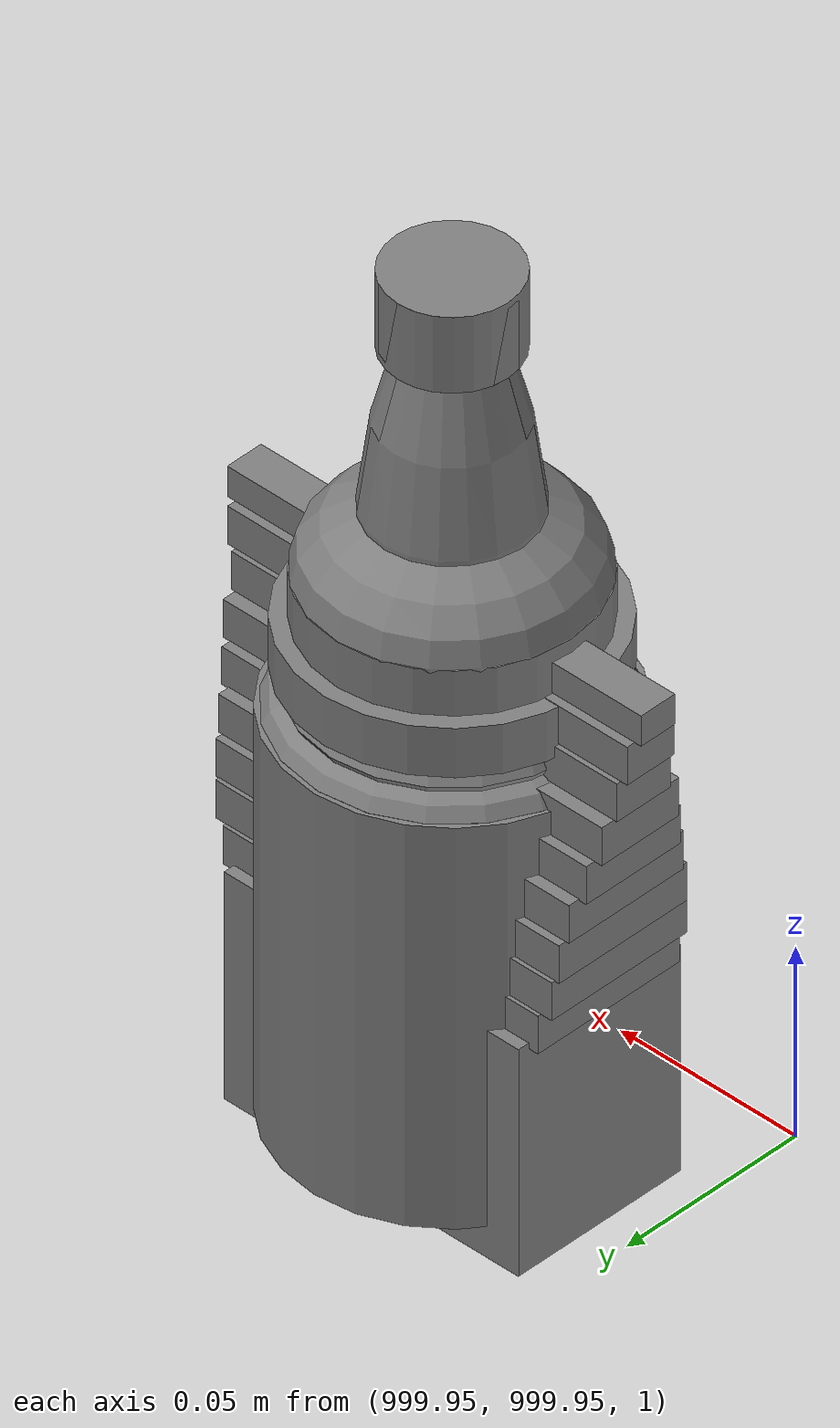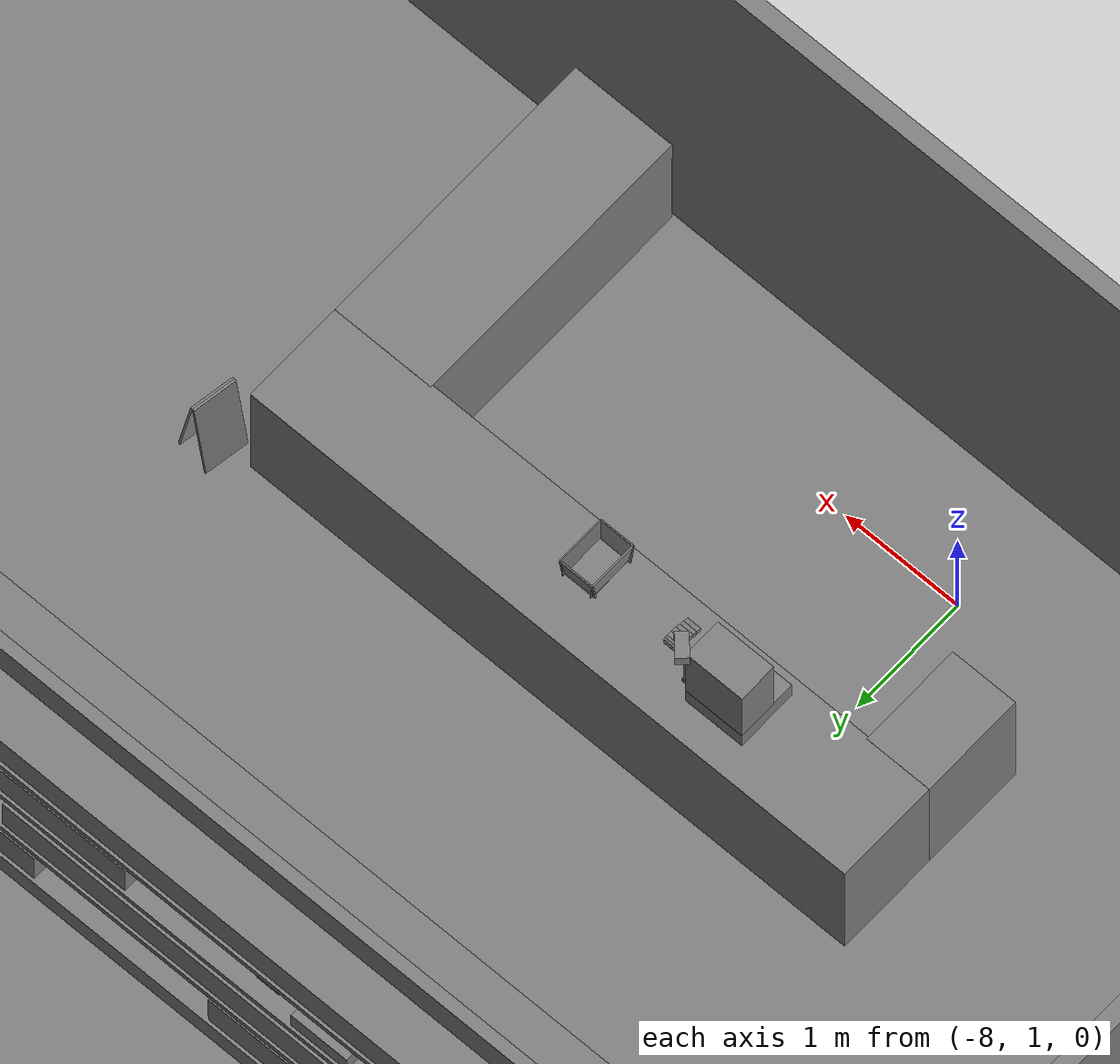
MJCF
<mujoco>
    <option gravity="0.000000000 0.000000000 -9.810000420" timestep="0.0166666" integrator="implicitfast" density="1.225" viscosity="1.8000001e-05" noslip_iterations="10" iterations="100" sdf_iterations="50">
        <flag multiccd="disable"/>
    </option>
    <size memory="1000M"/>
    <compiler coordinate="local"/>
    <worldbody>
        <light cutoff="30" pos="0 1 1" dir="0 -1 -2"/>
        <light cutoff="30" pos="0 -1 1" dir="0 1 -2"/>
        <body pos="0.000000000 0.000000000 0.000000000" euler="0.000000000 0.000000000 0.000000000" name="Interactive Objects_Interactive Objects"/>
        <body pos="1000.000000000 1000.000000000 1.000000000" euler="0.000000000 0.000000000 0.000000000" name="openloong_gripper_2f85_fix_base_usda_can">
            <geom contype="1" conaffinity="1" density="1000" type="cylinder" material="" rgba="0.500000000 0.500000000 0.500000000 1.000000000" solimp="0.899999976 0.949999988 0.001000000" friction="1.000000000 0.005000000 0.000100000" solref="0.020000000 1.000000000" margin="0" condim="3" group="0" pos="0.000000000 0.000000000 0.079676986" quat="1.000000000 0.000000000 0.000000000 0.000000000" size="0.034000002 0.071999997 1.000000000" name="openloong_gripper_2f85_fix_base_usda_geom_7B887656_1FEB_4DD8_8ECA_CB9140F40CBF"/>
            <geom contype="1" conaffinity="1" density="1000" type="ellipsoid" material="" rgba="0.500000000 0.500000000 0.500000000 1.000000000" solimp="0.899999976 0.949999988 0.001000000" friction="1.000000000 0.005000000 0.000100000" solref="0.020000000 1.000000000" margin="0" condim="3" group="0" pos="0.000000000 0.000000000 0.151854277" quat="1.000000000 0.000000000 0.000000000 0.000000000" size="0.034000002 0.034000002 0.020000000" name="openloong_gripper_2f85_fix_base_usda_geom_638E9A22_6359_4CFC_9147_5F2D2AC8E8AC"/>
            <geom contype="1" conaffinity="1" density="1000" type="box" material="" rgba="0.500000000 0.500000000 0.500000000 1.000000000" solimp="0.899999976 0.949999988 0.001000000" friction="1.000000000 0.005000000 0.000100000" solref="0.020000000 1.000000000" margin="0" condim="3" group="0" pos="0.000000000 0.000000000 0.004777670" quat="1.000000000 0.000000000 0.000000000 0.000000000" size="0.020000000 0.020000000 0.005000000" name="openloong_gripper_2f85_fix_base_usda_geom_4AE744BD_9AA1_48A1_9ACE_51B3605AACD4"/>
            <freejoint name="openloong_gripper_2f85_fix_base_usda_can_joint"/>
            <site size="0.005000000 0.005000000 0.005000000" rgba="0.500000000 0.500000000 0.500000000 1.000000000" pos="0.000000000 0.000000000 0.000000000" quat="1.000000000 0.000000000 0.000000000 0.000000000" group="0" type="sphere" name="openloong_gripper_2f85_fix_base_usda_cansite"/>
        </body>
        <body pos="1000.000000000 1000.000000000 1.000000000" euler="0.000000000 0.000000000 0.000000000" name="openloong_gripper_2f85_fix_base_usda_bottle_blue">
            <geom contype="1" conaffinity="1" density="1000" type="ellipsoid" material="" rgba="0.500000000 0.500000000 0.500000000 1.000000000" solimp="0.899999976 0.949999988 0.001000000" friction="1.000000000 0.005000000 0.000100000" solref="0.020000000 1.000000000" margin="0" condim="3" group="0" pos="0.000000000 0.000000000 0.118920922" quat="1.000000000 0.000000000 0.000000000 0.000000000" size="0.030999999 0.030999999 0.029999999" name="openloong_gripper_2f85_fix_base_usda_geom_DC7011C4_6F7C_4676_A801_FCB2FA09C000"/>
            <geom contype="1" conaffinity="1" density="1000" type="box" material="" rgba="0.500000000 0.500000000 0.500000000 1.000000000" solimp="0.899999976 0.949999988 0.001000000" friction="1.000000000 0.005000000 0.000100000" solref="0.020000000 1.000000000" margin="0" condim="3" group="0" pos="0.000000000 0.000000000 0.002164602" quat="1.000000000 0.000000000 0.000000000 0.000000000" size="0.020000000 0.020000000 0.003000000" name="openloong_gripper_2f85_fix_base_usda_geom_5BC130AD_D398_4D8C_A91C_BF421E94ABE6"/>
            <geom contype="1" conaffinity="1" density="1000" type="cylinder" material="" rgba="0.500000000 0.500000000 0.500000000 1.000000000" solimp="0.899999976 0.949999988 0.001000000" friction="1.000000000 0.005000000 0.000100000" solref="0.020000000 1.000000000" margin="0" condim="3" group="0" pos="0.000000000 -0.000366211 0.060859680" quat="1.000000000 0.000000000 0.000000000 0.000000000" size="0.030999999 0.057999998 1.000000000" name="openloong_gripper_2f85_fix_base_usda_geom_6294039E_9215_435C_8E59_229F9BB5137E"/>
            <geom contype="1" conaffinity="1" density="1000" type="cylinder" material="" rgba="0.500000000 0.500000000 0.500000000 1.000000000" solimp="0.899999976 0.949999988 0.001000000" friction="1.000000000 0.005000000 0.000100000" solref="0.020000000 1.000000000" margin="0" condim="3" group="0" pos="0.000000000 0.000000000 0.220594406" quat="1.000000000 0.000000000 0.000000000 0.000000000" size="0.016000001 0.010000000 1.000000000" name="openloong_gripper_2f85_fix_base_usda_geom_ED1CD200_03C0_40E6_B408_835697BE0E59"/>
            <geom contype="1" conaffinity="1" density="1000" type="ellipsoid" material="" rgba="0.500000000 0.500000000 0.500000000 1.000000000" solimp="0.899999976 0.949999988 0.001000000" friction="1.000000000 0.005000000 0.000100000" solref="0.020000000 1.000000000" margin="0" condim="3" group="0" pos="0.000000000 0.000000000 0.144259930" quat="1.000000000 0.000000000 0.000000000 0.000000000" size="0.021000000 0.021000000 0.079999998" name="openloong_gripper_2f85_fix_base_usda_geom_9FBA79D1_E24D_4963_820C_D1F052AE2DEA"/>
            <freejoint name="openloong_gripper_2f85_fix_base_usda_bottle_blue_joint"/>
            <site size="0.005000000 0.005000000 0.005000000" rgba="0.500000000 0.500000000 0.500000000 1.000000000" pos="0.000000000 0.000000000 0.000000000" quat="0.999961913 0.008726535 0.000000000 0.000000000" group="0" type="sphere" name="openloong_gripper_2f85_fix_base_usda_bottle_bluesite"/>
        </body>
        <body pos="-2.304804325 6.599555492 1.802629352" euler="-0.500260711 22.975929260 25.336450577" mocap="true" name="spotlight6_SpotLight"/>
        <body pos="1000.000000000 1000.000000000 1.000000000" euler="0.000000000 0.000000000 0.000000000" name="openloong_gripper_2f85_fix_base_usda_bottle_red">
            <geom contype="1" conaffinity="1" density="1000" type="ellipsoid" material="" rgba="0.500000000 0.500000000 0.500000000 1.000000000" solimp="0.899999976 0.949999988 0.001000000" friction="1.000000000 0.005000000 0.000100000" solref="0.020000000 1.000000000" margin="0" condim="3" group="0" pos="0.000000000 0.000000000 0.144284487" quat="1.000000000 0.000000000 0.000000000 0.000000000" size="0.021000000 0.021000000 0.079999998" name="openloong_gripper_2f85_fix_base_usda_geom_DDABA3CB_2473_4767_8796_557380F885C7"/>
            <geom contype="1" conaffinity="1" density="1000" type="cylinder" material="" rgba="0.500000000 0.500000000 0.500000000 1.000000000" solimp="0.899999976 0.949999988 0.001000000" friction="1.000000000 0.005000000 0.000100000" solref="0.020000000 1.000000000" margin="0" condim="3" group="0" pos="0.000000000 0.000000000 0.220618963" quat="1.000000000 0.000000000 0.000000000 0.000000000" size="0.016000001 0.010000000 1.000000000" name="openloong_gripper_2f85_fix_base_usda_geom_181B1474_B87A_4661_93AA_B251BDB98122"/>
            <geom contype="1" conaffinity="1" density="1000" type="ellipsoid" material="" rgba="0.500000000 0.500000000 0.500000000 1.000000000" solimp="0.899999976 0.949999988 0.001000000" friction="1.000000000 0.005000000 0.000100000" solref="0.020000000 1.000000000" margin="0" condim="3" group="0" pos="0.000000000 0.000000000 0.118945479" quat="1.000000000 0.000000000 0.000000000 0.000000000" size="0.030999999 0.030999999 0.029999999" name="openloong_gripper_2f85_fix_base_usda_geom_9E6525ED_1318_4AD4_BC2A_F375379DC1CF"/>
            <geom contype="1" conaffinity="1" density="1000" type="box" material="" rgba="0.500000000 0.500000000 0.500000000 1.000000000" solimp="0.899999976 0.949999988 0.001000000" friction="1.000000000 0.005000000 0.000100000" solref="0.020000000 1.000000000" margin="0" condim="3" group="0" pos="0.000000000 0.000000000 0.002189159" quat="1.000000000 0.000000000 0.000000000 0.000000000" size="0.020000000 0.020000000 0.003000000" name="openloong_gripper_2f85_fix_base_usda_geom_1E62C46C_214D_4E42_8354_F4372E964E51"/>
            <geom contype="1" conaffinity="1" density="1000" type="cylinder" material="" rgba="0.500000000 0.500000000 0.500000000 1.000000000" solimp="0.899999976 0.949999988 0.001000000" friction="1.000000000 0.005000000 0.000100000" solref="0.020000000 1.000000000" margin="0" condim="3" group="0" pos="0.000000000 -0.000366211 0.060884237" quat="1.000000000 0.000000000 0.000000000 0.000000000" size="0.030999999 0.057999998 1.000000000" name="openloong_gripper_2f85_fix_base_usda_geom_446B6125_6856_442B_9ECE_009739EA1444"/>
            <freejoint name="openloong_gripper_2f85_fix_base_usda_bottle_red_joint"/>
            <site size="0.005000000 0.005000000 0.005000000" rgba="0.500000000 0.500000000 0.500000000 1.000000000" pos="0.000000000 0.000000000 0.000000000" quat="0.999961913 0.008726535 0.000000000 0.000000000" group="0" type="sphere" name="openloong_gripper_2f85_fix_base_usda_bottle_redsite"/>
        </body>
        <body pos="-2.103526592 5.968920231 1.802757263" euler="24.888195038 -64.147590637 -2.475954771" mocap="true" name="spotlight4_SpotLight"/>
        <body pos="1000.000000000 1000.000000000 1.000000000" euler="0.000000000 0.000000000 0.000000000" name="openloong_gripper_2f85_fix_base_usda_jar_01">
            <geom contype="1" conaffinity="1" density="1000" type="box" material="" rgba="0.500000000 0.500000000 0.500000000 1.000000000" solimp="0.899999976 0.949999988 0.001000000" friction="1.000000000 0.005000000 0.000100000" solref="0.020000000 1.000000000" margin="0" condim="3" group="0" pos="0.000000000 0.000000000 0.006158113" quat="1.000000000 0.000000000 0.000000000 0.000000000" size="0.020000000 0.020000000 0.005000000" name="openloong_gripper_2f85_fix_base_usda_geom_EFA9EEC0_C0E6_4BB4_93AE_B9A9F23FBAA3"/>
            <geom contype="1" conaffinity="1" density="1000" type="cylinder" material="" rgba="0.500000000 0.500000000 0.500000000 1.000000000" solimp="0.899999976 0.949999988 0.001000000" friction="1.000000000 0.005000000 0.000100000" solref="0.020000000 1.000000000" margin="0" condim="3" group="0" pos="0.000000000 0.000000000 0.062744498" quat="1.000000000 0.000000000 0.000000000 0.000000000" size="0.041000001 0.052999999 1.000000000" name="openloong_gripper_2f85_fix_base_usda_geom_7FBCFB3F_8F78_4E65_8670_A889B1710022"/>
            <geom contype="1" conaffinity="1" density="1000" type="ellipsoid" material="" rgba="0.500000000 0.500000000 0.500000000 1.000000000" solimp="0.899999976 0.949999988 0.001000000" friction="1.000000000 0.005000000 0.000100000" solref="0.020000000 1.000000000" margin="0" condim="3" group="0" pos="0.000000000 0.000000000 0.122252703" quat="1.000000000 0.000000000 0.000000000 0.000000000" size="0.035999998 0.035999998 0.010000000" name="openloong_gripper_2f85_fix_base_usda_geom_BC58BF79_9050_4384_8A00_FBA4CFC9F97B"/>
            <geom contype="1" conaffinity="1" density="1000" type="cylinder" material="" rgba="0.500000000 0.500000000 0.500000000 1.000000000" solimp="0.899999976 0.949999988 0.001000000" friction="1.000000000 0.005000000 0.000100000" solref="0.020000000 1.000000000" margin="0" condim="3" group="0" pos="0.000000000 0.000000000 0.015747190" quat="1.000000000 0.000000000 0.000000000 0.000000000" size="0.035000000 0.010000000 1.000000000" name="openloong_gripper_2f85_fix_base_usda_geom_74224F86_A25F_45D1_B2A2_AC01888F68DF"/>
            <geom contype="1" conaffinity="1" density="1000" type="ellipsoid" material="" rgba="0.500000000 0.500000000 0.500000000 1.000000000" solimp="0.899999976 0.949999988 0.001000000" friction="1.000000000 0.005000000 0.000100000" solref="0.020000000 1.000000000" margin="0" condim="3" group="0" pos="0.000000000 0.000000000 0.115815401" quat="1.000000000 0.000000000 0.000000000 0.000000000" size="0.039999999 0.039999999 0.010000000" name="openloong_gripper_2f85_fix_base_usda_geom_C7C55F34_C977_4785_B743_8202FE79C9F9"/>
            <geom contype="1" conaffinity="1" density="1000" type="cylinder" material="" rgba="0.500000000 0.500000000 0.500000000 1.000000000" solimp="0.899999976 0.949999988 0.001000000" friction="1.000000000 0.005000000 0.000100000" solref="0.020000000 1.000000000" margin="0" condim="3" group="0" pos="0.000000000 0.000000000 0.133183479" quat="1.000000000 0.000000000 0.000000000 0.000000000" size="0.037999999 0.006500000 1.000000000" name="openloong_gripper_2f85_fix_base_usda_geom_32E41233_1244_4D78_9425_A011E4C7BC56"/>
            <freejoint name="openloong_gripper_2f85_fix_base_usda_jar_01_joint"/>
            <site size="0.005000000 0.005000000 0.005000000" rgba="0.500000000 0.500000000 0.500000000 1.000000000" pos="0.000000000 0.000000000 0.000000000" quat="1.000000000 0.000000000 0.000000000 0.000000000" group="0" type="sphere" name="openloong_gripper_2f85_fix_base_usda_jar_01site"/>
        </body>
        <body pos="-1.981205225 6.021731377 1.699029088" euler="-92.485900879 -34.856227875 -135.079620361" mocap="true" name="spotlight5_SpotLight"/>
        <body pos="1000.000000000 1000.000000000 1.000000000" euler="0.000000000 0.000000000 0.000000000" name="openloong_gripper_2f85_fix_base_usda_salt">
            <geom contype="1" conaffinity="1" density="1000" type="box" material="" rgba="0.500000000 0.500000000 0.500000000 1.000000000" solimp="0.899999976 0.949999988 0.001000000" friction="1.000000000 0.005000000 0.000100000" solref="0.020000000 1.000000000" margin="0" condim="3" group="0" pos="0.000305176 0.000000000 0.084862232" quat="1.000000000 0.000000000 0.000000000 0.000000000" size="0.048999999 0.018999999 0.005000000" name="openloong_gripper_2f85_fix_base_usda_geom_E6FD26FF_F3D5_47F9_A7ED_FCCBB1A6A2B7"/>
            <geom contype="1" conaffinity="1" density="1000" type="box" material="" rgba="0.500000000 0.500000000 0.500000000 1.000000000" solimp="0.899999976 0.949999988 0.001000000" friction="1.000000000 0.005000000 0.000100000" solref="0.020000000 1.000000000" margin="0" condim="3" group="0" pos="0.000305176 0.000000000 0.104564309" quat="1.000000000 0.000000000 0.000000000 0.000000000" size="0.052000001 0.014000000 0.005000000" name="openloong_gripper_2f85_fix_base_usda_geom_9D53848A_9F86_46C9_9D92_E571C4C908B1"/>
            <geom contype="1" conaffinity="1" density="1000" type="box" material="" rgba="0.500000000 0.500000000 0.500000000 1.000000000" solimp="0.899999976 0.949999988 0.001000000" friction="1.000000000 0.005000000 0.000100000" solref="0.020000000 1.000000000" margin="0" condim="3" group="0" pos="0.000305176 0.000000000 0.114487171" quat="1.000000000 0.000000000 0.000000000 0.000000000" size="0.054000001 0.011500000 0.005000000" name="openloong_gripper_2f85_fix_base_usda_geom_8EAD881C_495F_4F6A_8FB9_9A845A8D7BBA"/>
            <geom contype="1" conaffinity="1" density="1000" type="box" material="" rgba="0.500000000 0.500000000 0.500000000 1.000000000" solimp="0.899999976 0.949999988 0.001000000" friction="1.000000000 0.005000000 0.000100000" solref="0.020000000 1.000000000" margin="0" condim="3" group="0" pos="0.000305176 0.000000000 0.075103164" quat="1.000000000 0.000000000 0.000000000 0.000000000" size="0.048000000 0.020000000 0.005000000" name="openloong_gripper_2f85_fix_base_usda_geom_C356798D_A2E8_448B_88EA_C26B52D8154C"/>
            <geom contype="1" conaffinity="1" density="1000" type="box" material="" rgba="0.500000000 0.500000000 0.500000000 1.000000000" solimp="0.899999976 0.949999988 0.001000000" friction="1.000000000 0.005000000 0.000100000" solref="0.020000000 1.000000000" margin="0" condim="3" group="0" pos="0.000305176 0.000000000 0.134892464" quat="1.000000000 0.000000000 0.000000000 0.000000000" size="0.057000000 0.007000000 0.005000000" name="openloong_gripper_2f85_fix_base_usda_geom_194695A0_E880_41D5_9D61_AB19883A14E5"/>
            <geom contype="1" conaffinity="1" density="1000" type="box" material="" rgba="0.500000000 0.500000000 0.500000000 1.000000000" solimp="0.899999976 0.949999988 0.001000000" friction="1.000000000 0.005000000 0.000100000" solref="0.020000000 1.000000000" margin="0" condim="3" group="0" pos="0.000305176 0.000000000 0.094920278" quat="1.000000000 0.000000000 0.000000000 0.000000000" size="0.050000001 0.017000001 0.005000000" name="openloong_gripper_2f85_fix_base_usda_geom_29FC9C4D_4E95_41E8_A095_ED10E3FE16D8"/>
            <geom contype="1" conaffinity="1" density="1000" type="box" material="" rgba="0.500000000 0.500000000 0.500000000 1.000000000" solimp="0.899999976 0.949999988 0.001000000" friction="1.000000000 0.005000000 0.000100000" solref="0.020000000 1.000000000" margin="0" condim="3" group="0" pos="0.000305176 0.000000000 0.065204859" quat="1.000000000 0.000000000 0.000000000 0.000000000" size="0.045000002 0.021000000 0.005000000" name="openloong_gripper_2f85_fix_base_usda_geom_67327525_0D45_4408_A19E_0261271D7ECD"/>
            <geom contype="1" conaffinity="1" density="1000" type="box" material="" rgba="0.500000000 0.500000000 0.500000000 1.000000000" solimp="0.899999976 0.949999988 0.001000000" friction="1.000000000 0.005000000 0.000100000" solref="0.020000000 1.000000000" margin="0" condim="3" group="0" pos="0.000305176 0.000000000 0.144135714" quat="1.000000000 0.000000000 0.000000000 0.000000000" size="0.059000000 0.005000000 0.004000000" name="openloong_gripper_2f85_fix_base_usda_geom_6578C25D_CE63_481C_AC0B_A4A640D6245D"/>
            <geom contype="1" conaffinity="1" density="1000" type="box" material="" rgba="0.500000000 0.500000000 0.500000000 1.000000000" solimp="0.899999976 0.949999988 0.001000000" friction="1.000000000 0.005000000 0.000100000" solref="0.020000000 1.000000000" margin="0" condim="3" group="0" pos="0.000000000 0.000000000 0.031593561" quat="1.000000000 0.000000000 0.000000000 0.000000000" size="0.041999999 0.024000000 0.029999999" name="openloong_gripper_2f85_fix_base_usda_geom_66D06DEB_27B4_440C_B100_12DA7EA57966"/>
            <geom contype="1" conaffinity="1" density="1000" type="box" material="" rgba="0.500000000 0.500000000 0.500000000 1.000000000" solimp="0.899999976 0.949999988 0.001000000" friction="1.000000000 0.005000000 0.000100000" solref="0.020000000 1.000000000" margin="0" condim="3" group="0" pos="0.000305176 0.000000000 0.124608755" quat="1.000000000 0.000000000 0.000000000 0.000000000" size="0.055000000 0.008000000 0.005000000" name="openloong_gripper_2f85_fix_base_usda_geom_C91462EE_E420_4858_8465_A70620919EF8"/>
            <freejoint name="openloong_gripper_2f85_fix_base_usda_salt_joint"/>
            <site size="0.005000000 0.005000000 0.005000000" rgba="0.500000000 0.500000000 0.500000000 1.000000000" pos="0.000000000 0.000000000 0.000000000" quat="1.000000000 0.000000000 0.000000000 0.000000000" group="0" type="sphere" name="openloong_gripper_2f85_fix_base_usda_saltsite"/>
        </body>
        <body pos="0.000000000 0.000000000 0.000000000" euler="0.000000000 0.000000000 0.000000000" name=" Static Objects_ Static Objects">
            <geom contype="1" conaffinity="1" density="1000" type="box" material="" rgba="0.500000000 0.500000000 0.500000000 1.000000000" solimp="0.899999976 0.949999988 0.001000000" friction="1.000000000 0.005000000 0.000100000" solref="0.020000000 1.000000000" margin="0" condim="3" group="0" pos="-3.101639986 6.150595188 1.018643856" quat="1.000000000 0.000000000 0.000000000 0.000000000" size="0.050000001 0.579999983 1.019999981" name=" Static Objects_geom_EB8F47F1_0B6F_412D_921F_F82147CD52EC"/>
            <geom contype="1" conaffinity="1" density="1000" type="box" material="" rgba="0.500000000 0.500000000 0.500000000 1.000000000" solimp="0.899999976 0.949999988 0.001000000" friction="1.000000000 0.005000000 0.000100000" solref="0.020000000 1.000000000" margin="0" condim="3" group="0" pos="-2.825197220 6.153595448 1.115278244" quat="0.707107067 0.000000000 0.000000000 0.707106471" size="0.550000012 0.239999995 0.025000000" name=" Static Objects_geom_DD30DD30_C95B_47B2_8CB3_D82EE923BD12"/>
            <geom contype="1" conaffinity="1" density="1000" type="box" material="" rgba="0.500000000 0.500000000 0.500000000 1.000000000" solimp="0.899999976 0.949999988 0.001000000" friction="1.000000000 0.005000000 0.000100000" solref="0.020000000 1.000000000" margin="0" condim="3" group="0" pos="-2.825197220 6.153595448 0.097434282" quat="0.707107067 0.000000000 0.000000000 0.707106471" size="0.550000012 0.239999995 0.098999999" name=" Static Objects_geom_2F301FD6_0E9F_47BD_9A45_1A623126B5AE"/>
            <geom contype="1" conaffinity="1" density="1000" type="box" material="" rgba="0.500000000 0.500000000 0.500000000 1.000000000" solimp="0.899999976 0.949999988 0.001000000" friction="1.000000000 0.005000000 0.000100000" solref="0.020000000 1.000000000" margin="0" condim="3" group="0" pos="-6.293097973 6.153595448 1.114443064" quat="0.707107067 0.000000000 0.000000000 0.707106471" size="0.529999971 3.134999990 0.025000000" name=" Static Objects_geom_819052A7_7751_4177_882A_5680A4984E2D"/>
            <geom contype="1" conaffinity="1" density="1000" type="box" material="" rgba="0.500000000 0.500000000 0.500000000 1.000000000" solimp="0.899999976 0.949999988 0.001000000" friction="1.000000000 0.005000000 0.000100000" solref="0.020000000 1.000000000" margin="0" condim="3" group="0" pos="-6.286010742 6.153595448 0.096129179" quat="0.707107067 0.000000000 0.000000000 0.707106471" size="0.529999971 3.134999990 0.098999999" name=" Static Objects_geom_8AD61F98_E25A_4379_BA19_20666791CC89"/>
            <geom contype="1" conaffinity="1" density="1000" type="box" material="" rgba="0.500000000 0.500000000 0.500000000 1.000000000" solimp="0.899999976 0.949999988 0.001000000" friction="1.000000000 0.005000000 0.000100000" solref="0.020000000 1.000000000" margin="0" condim="3" group="0" pos="-2.825197220 6.153595448 1.563861728" quat="0.707107067 0.000000000 0.000000000 0.707106471" size="0.550000012 0.239999995 0.025000000" name=" Static Objects_geom_0DEC1FB6_18D5_46DA_908B_7FFF8A03C74F"/>
            <geom contype="1" conaffinity="1" density="1000" type="box" material="" rgba="0.500000000 0.500000000 0.500000000 1.000000000" solimp="0.899999976 0.949999988 0.001000000" friction="1.000000000 0.005000000 0.000100000" solref="0.020000000 1.000000000" margin="0" condim="3" group="0" pos="-6.311686516 6.153595448 1.018643856" quat="0.707107067 0.000000000 0.000000000 0.707106471" size="0.050000001 3.150000095 1.019999981" name=" Static Objects_geom_7AE6C418_80D1_4B2B_9FA7_379AB88932CF"/>
            <geom contype="1" conaffinity="1" density="1000" type="box" material="" rgba="0.500000000 0.500000000 0.500000000 1.000000000" solimp="0.899999976 0.949999988 0.001000000" friction="1.000000000 0.005000000 0.000100000" solref="0.020000000 1.000000000" margin="0" condim="3" group="0" pos="-2.825197220 6.153595448 0.629031777" quat="0.707107067 0.000000000 0.000000000 0.707106471" size="0.550000012 0.239999995 0.025000000" name=" Static Objects_geom_B9D08450_D2C2_4CF4_8392_91BBDEEF7944"/>
            <geom contype="1" conaffinity="1" density="1000" type="box" material="" rgba="0.500000000 0.500000000 0.500000000 1.000000000" solimp="0.899999976 0.949999988 0.001000000" friction="1.000000000 0.005000000 0.000100000" solref="0.020000000 1.000000000" margin="0" condim="3" group="0" pos="-6.286010742 6.153595448 1.563861728" quat="0.707107067 0.000000000 0.000000000 0.707106471" size="0.529999971 3.134999990 0.025000000" name=" Static Objects_geom_E73EFBFD_A537_4A3E_89FB_1131D6760E1D"/>
            <geom contype="1" conaffinity="1" density="1000" type="box" material="" rgba="0.500000000 0.500000000 0.500000000 1.000000000" solimp="0.899999976 0.949999988 0.001000000" friction="1.000000000 0.005000000 0.000100000" solref="0.020000000 1.000000000" margin="0" condim="3" group="0" pos="-6.286010742 6.153595448 0.629031777" quat="0.707107067 0.000000000 0.000000000 0.707106471" size="0.529999971 3.134999990 0.025000000" name=" Static Objects_geom_6118BB64_32BF_4AB9_A434_F9B8BBF46DEB"/>
            <geom contype="1" conaffinity="1" density="1000" type="box" material="" rgba="0.500000000 0.500000000 0.500000000 1.000000000" solimp="0.899999976 0.949999988 0.001000000" friction="1.000000000 0.005000000 0.000100000" solref="0.020000000 1.000000000" margin="0" condim="3" group="0" pos="-7.719123363 2.867671013 1.173410416" quat="1.000000000 0.000000000 0.000000000 0.000000000" size="0.250000000 0.250000000 0.079999998" name=" Static Objects_geom_AF980679_6051_4A24_A923_131A31884EB0"/>
            <geom contype="1" conaffinity="1" density="1000" type="box" material="" rgba="0.500000000 0.500000000 0.500000000 1.000000000" solimp="0.899999976 0.949999988 0.001000000" friction="1.000000000 0.005000000 0.000100000" solref="0.020000000 1.000000000" margin="0" condim="3" group="0" pos="-7.408766270 3.088089943 1.776644945" quat="0.928051054 0.000000000 0.000000000 0.372453064" size="0.050000001 0.100000001 0.050000001" name=" Static Objects_geom_2CBDBDB3_415B_4174_96D6_DEC7EBAFCE32"/>
            <geom contype="1" conaffinity="1" density="1000" type="box" material="" rgba="0.500000000 0.500000000 0.500000000 1.000000000" solimp="0.899999976 0.949999988 0.001000000" friction="1.000000000 0.005000000 0.000100000" solref="0.020000000 1.000000000" margin="0" condim="3" group="0" pos="-7.719123363 2.958004713 1.530241251" quat="1.000000000 0.000000000 0.000000000 0.000000000" size="0.250000000 0.159999996 0.280000001" name=" Static Objects_geom_28833EAE_3454_4E45_8B6C_4C499DE6F2B8"/>
            <geom contype="1" conaffinity="1" density="1000" type="cylinder" material="" rgba="0.500000000 0.500000000 0.500000000 1.000000000" solimp="0.899999976 0.949999988 0.001000000" friction="1.000000000 0.005000000 0.000100000" solref="0.020000000 1.000000000" margin="0" condim="3" group="0" pos="-7.427312374 3.069516420 1.502544641" quat="0.928051054 0.000000000 0.000000000 0.372453064" size="0.015000000 0.230000004 0.100000001" name=" Static Objects_geom_6443F178_8050_4A12_9F40_2AD842B4AD03"/>
            <geom contype="1" conaffinity="1" density="1000" type="box" material="" rgba="0.500000000 0.500000000 0.500000000 1.000000000" solimp="0.899999976 0.949999988 0.001000000" friction="1.000000000 0.005000000 0.000100000" solref="0.020000000 1.000000000" margin="0" condim="3" group="0" pos="-7.437745571 3.067511320 1.289965630" quat="1.000000000 0.000000000 0.000000000 0.000000000" size="0.029999999 0.020000000 0.020000000" name=" Static Objects_geom_308E1FA0_D441_457A_AB79_DB5916180F47"/>
            <geom contype="1" conaffinity="1" density="1000" type="box" material="" rgba="0.500000000 0.500000000 0.500000000 1.000000000" solimp="0.899999976 0.949999988 0.001000000" friction="1.000000000 0.005000000 0.000100000" solref="0.020000000 1.000000000" margin="0" condim="3" group="0" pos="-9.058088303 6.434794426 1.209077358" quat="1.000000000 0.000000000 0.000000000 0.000000000" size="0.250000000 0.100000001 0.070000000" name=" Static Objects_geom_3DF5C426_10E2_4928_A13F_D41B7E641562"/>
            <geom contype="1" conaffinity="1" density="1000" type="box" material="" rgba="0.500000000 0.500000000 0.500000000 1.000000000" solimp="0.899999976 0.949999988 0.001000000" friction="1.000000000 0.005000000 0.000100000" solref="0.020000000 1.000000000" margin="0" condim="3" group="0" pos="-7.886891365 6.459744930 0.352518857" quat="1.000000000 0.000000000 0.000000000 0.000000000" size="1.500000000 0.200000003 0.150000006" name=" Static Objects_geom_E82CDD9E_91D6_41DF_A70C_F58771C884D4"/>
            <geom contype="1" conaffinity="1" density="1000" type="box" material="" rgba="0.500000000 0.500000000 0.500000000 1.000000000" solimp="0.899999976 0.949999988 0.001000000" friction="1.000000000 0.005000000 0.000100000" solref="0.020000000 1.000000000" margin="0" condim="3" group="0" pos="-9.237723351 6.464855671 1.209077358" quat="1.000000000 0.000000000 0.000000000 0.000000000" size="0.100000001 0.100000001 0.070000000" name=" Static Objects_geom_FB001915_C961_43A3_87BC_62BE252FC797"/>
            <geom contype="1" conaffinity="1" density="1000" type="box" material="" rgba="0.500000000 0.500000000 0.500000000 1.000000000" solimp="0.899999976 0.949999988 0.001000000" friction="1.000000000 0.005000000 0.000100000" solref="0.020000000 1.000000000" margin="0" condim="3" group="0" pos="-6.924745083 6.362090111 1.214329123" quat="1.000000000 0.000000000 0.000000000 0.000000000" size="0.200000003 0.100000001 0.075000003" name=" Static Objects_geom_C60C8B94_2EBA_4E40_B25B_1D7465AD7826"/>
            <geom contype="1" conaffinity="1" density="1000" type="box" material="" rgba="0.500000000 0.500000000 0.500000000 1.000000000" solimp="0.899999976 0.949999988 0.001000000" friction="1.000000000 0.005000000 0.000100000" solref="0.020000000 1.000000000" margin="0" condim="3" group="0" pos="-4.407354832 6.459744930 1.292199373" quat="1.000000000 0.000000000 0.000000000 0.000000000" size="1.240000010 0.200000003 0.150000006" name=" Static Objects_geom_3DC53044_CF4D_41B0_9029_56E2D48CAFDE"/>
            <geom contype="1" conaffinity="1" density="1000" type="box" material="" rgba="0.500000000 0.500000000 0.500000000 1.000000000" solimp="0.899999976 0.949999988 0.001000000" friction="1.000000000 0.005000000 0.000100000" solref="0.020000000 1.000000000" margin="0" condim="3" group="0" pos="-5.611940861 6.318420410 0.350975692" quat="1.000000000 0.000000000 0.000000000 0.000000000" size="0.699999988 0.100000001 0.150000006" name=" Static Objects_geom_B755D010_0897_4EA7_8F1A_97BCBF6F01B9"/>
            <geom contype="1" conaffinity="1" density="1000" type="box" material="" rgba="0.500000000 0.500000000 0.500000000 1.000000000" solimp="0.899999976 0.949999988 0.001000000" friction="1.000000000 0.005000000 0.000100000" solref="0.020000000 1.000000000" margin="0" condim="3" group="0" pos="-6.300771236 6.459744930 1.744376063" quat="1.000000000 0.000000000 0.000000000 0.000000000" size="3.000000000 0.200000003 0.150000006" name=" Static Objects_geom_070B7BC2_69F2_4F13_A2AB_D9EF9F9FBCE0"/>
            <geom contype="1" conaffinity="1" density="1000" type="box" material="" rgba="0.500000000 0.500000000 0.500000000 1.000000000" solimp="0.899999976 0.949999988 0.001000000" friction="1.000000000 0.005000000 0.000100000" solref="0.020000000 1.000000000" margin="0" condim="3" group="0" pos="-6.751636982 6.459744930 0.800981164" quat="1.000000000 0.000000000 0.000000000 0.000000000" size="2.200000048 0.200000003 0.150000006" name=" Static Objects_geom_134D34F2_2199_4705_A343_175F234269BC"/>
            <geom contype="1" conaffinity="1" density="1000" type="box" material="" rgba="0.500000000 0.500000000 0.500000000 1.000000000" solimp="0.899999976 0.949999988 0.001000000" friction="1.000000000 0.005000000 0.000100000" solref="0.020000000 1.000000000" margin="0" condim="3" group="0" pos="-8.844120979 6.464855671 1.209077358" quat="1.000000000 0.000000000 0.000000000 0.000000000" size="0.100000001 0.100000001 0.070000000" name=" Static Objects_geom_6A26472D_3480_4551_BD06_B6F1A121F5FC"/>
            <geom contype="1" conaffinity="1" density="1000" type="box" material="" rgba="0.500000000 0.500000000 0.500000000 1.000000000" solimp="0.899999976 0.949999988 0.001000000" friction="1.000000000 0.005000000 0.000100000" solref="0.020000000 1.000000000" margin="0" condim="3" group="0" pos="-6.098561764 6.327973843 1.292199373" quat="1.000000000 0.000000000 0.000000000 0.000000000" size="0.500000000 0.100000001 0.150000006" name=" Static Objects_geom_1C8882A2_F5D3_46E8_9969_5A4D9A1F394B"/>
            <geom contype="1" conaffinity="1" density="1000" type="box" material="" rgba="0.500000000 0.500000000 0.500000000 1.000000000" solimp="0.899999976 0.949999988 0.001000000" friction="1.000000000 0.005000000 0.000100000" solref="0.020000000 1.000000000" margin="0" condim="3" group="0" pos="-6.824534416 6.447464466 1.212718010" quat="1.000000000 0.000000000 0.000000000 0.000000000" size="0.100000001 0.100000001 0.075000003" name=" Static Objects_geom_1808DD17_63CE_4F5C_A4C9_2153A55BD2F7"/>
            <geom contype="1" conaffinity="1" density="1000" type="box" material="" rgba="0.500000000 0.500000000 0.500000000 1.000000000" solimp="0.899999976 0.949999988 0.001000000" friction="1.000000000 0.005000000 0.000100000" solref="0.020000000 1.000000000" margin="0" condim="3" group="0" pos="-3.907610416 6.318625927 0.800981164" quat="1.000000000 0.000000000 0.000000000 0.000000000" size="0.500000000 0.100000001 0.150000006" name=" Static Objects_geom_A019CBEC_7155_42CF_A3A7_396687374E7A"/>
            <geom contype="1" conaffinity="1" density="1000" type="box" material="" rgba="0.500000000 0.500000000 0.500000000 1.000000000" solimp="0.899999976 0.949999988 0.001000000" friction="1.000000000 0.005000000 0.000100000" solref="0.020000000 1.000000000" margin="0" condim="3" group="0" pos="-7.373087406 6.458900928 1.214329123" quat="1.000000000 0.000000000 0.000000000 0.000000000" size="0.250000000 0.200000003 0.075000003" name=" Static Objects_geom_4EBC8D46_F0F4_46FB_86C1_C9AF51750E05"/>
            <geom contype="1" conaffinity="1" density="1000" type="box" material="" rgba="0.500000000 0.500000000 0.500000000 1.000000000" solimp="0.899999976 0.949999988 0.001000000" friction="1.000000000 0.005000000 0.000100000" solref="0.020000000 1.000000000" margin="0" condim="3" group="0" pos="-4.035642624 6.459744930 0.352518857" quat="1.000000000 0.000000000 0.000000000 0.000000000" size="0.800000012 0.200000003 0.150000006" name=" Static Objects_geom_503745F8_01EB_4C4D_A7A9_DB374D96388E"/>
            <geom contype="1" conaffinity="1" density="1000" type="box" material="" rgba="0.500000000 0.500000000 0.500000000 1.000000000" solimp="0.899999976 0.949999988 0.001000000" friction="1.000000000 0.005000000 0.000100000" solref="0.020000000 1.000000000" margin="0" condim="3" group="0" pos="-6.460197449 2.937205315 0.548931718" quat="1.000000000 0.000000000 0.000000000 0.000000000" size="2.650000095 0.430000007 0.550000012" name=" Static Objects_geom_BA5F1B66_3C91_4006_A564_D74E9BA17283"/>
            <geom contype="1" conaffinity="1" density="1000" type="box" material="" rgba="0.500000000 0.500000000 0.500000000 1.000000000" solimp="0.899999976 0.949999988 0.001000000" friction="1.000000000 0.005000000 0.000100000" solref="0.020000000 1.000000000" margin="0" condim="3" group="0" pos="-4.240264893 1.327049494 0.549888909" quat="1.000000000 0.000000000 0.000000000 0.000000000" size="0.430000007 1.200000048 0.550000012" name=" Static Objects_geom_88FA8C12_B1C3_484A_9A9B_798DE9090677"/>
            <geom contype="1" conaffinity="1" density="1000" type="box" material="" rgba="0.500000000 0.500000000 0.500000000 1.000000000" solimp="0.899999976 0.949999988 0.001000000" friction="1.000000000 0.005000000 0.000100000" solref="0.020000000 1.000000000" margin="0" condim="3" group="0" pos="-8.830721855 2.096410990 0.549305558" quat="1.000000000 0.000000000 0.000000000 0.000000000" size="0.280000001 0.430000007 0.550000012" name=" Static Objects_geom_AA54DE0E_A98D_480B_A05F_C5AAF03B2AC7"/>
            <geom contype="1" conaffinity="1" density="1000" type="plane" material="" rgba="0.500000000 0.500000000 0.500000000 1.000000000" solimp="0.899999976 0.949999988 0.001000000" friction="1.000000000 0.005000000 0.000100000" solref="0.020000000 1.000000000" margin="0" condim="3" group="0" pos="-6.000000000 10.399999619 0.000000000" quat="1.000000000 0.000000000 0.000000000 0.000000000" size="6.050000191 10.800000191 0.010000000" name=" Static Objects_geom_CD883805_1A77_4C7A_917B_06D7EC24244B"/>
            <geom contype="1" conaffinity="1" density="1000" type="box" material="" rgba="0.500000000 0.500000000 0.500000000 1.000000000" solimp="0.899999976 0.949999988 0.001000000" friction="1.000000000 0.005000000 0.000100000" solref="0.020000000 1.000000000" margin="0" condim="3" group="0" pos="-6.000000000 0.035000000 2.000000000" quat="1.000000000 0.000000000 0.000000000 0.000000000" size="6.079999924 0.070000000 2.000000000" name=" Static Objects_geom_6EF9864A_0102_46D0_99C5_17955CB5893B"/>
            <geom contype="1" conaffinity="1" density="1000" type="box" material="" rgba="0.500000000 0.500000000 0.500000000 1.000000000" solimp="0.899999976 0.949999988 0.001000000" friction="1.000000000 0.005000000 0.000100000" solref="0.020000000 1.000000000" margin="0" condim="3" group="0" pos="-6.000000000 20.159999847 2.000000000" quat="1.000000000 0.000000000 0.000000000 0.000000000" size="6.079999924 0.070000000 2.000000000" name=" Static Objects_geom_075F6224_3D8F_4AF3_AF73_5D22E27B2312"/>
            <geom contype="1" conaffinity="1" density="1000" type="box" material="" rgba="0.500000000 0.500000000 0.500000000 1.000000000" solimp="0.899999976 0.949999988 0.001000000" friction="1.000000000 0.005000000 0.000100000" solref="0.020000000 1.000000000" margin="0" condim="3" group="0" pos="0.000000000 10.000000000 2.000000000" quat="1.000000000 0.000000000 0.000000000 0.000000000" size="0.070000000 10.500000000 2.000000000" name=" Static Objects_geom_F44338FB_E87F_4960_A17C_D4C0A20FC11C"/>
            <geom contype="1" conaffinity="1" density="1000" type="box" material="" rgba="0.500000000 0.500000000 0.500000000 1.000000000" solimp="0.899999976 0.949999988 0.001000000" friction="1.000000000 0.005000000 0.000100000" solref="0.020000000 1.000000000" margin="0" condim="3" group="0" pos="-12.050000191 10.000000000 2.000000000" quat="1.000000000 0.000000000 0.000000000 0.000000000" size="0.070000000 10.500000000 2.000000000" name=" Static Objects_geom_D3DBFF85_20D0_40F5_9F95_F6789ACA7AC6"/>
        </body>
        <body pos="-3.510578632 3.403555870 -0.000000100" euler="0.000000000 0.000000000 40.200675964" name="openloong_gripper_2f85_fix_base_usda_PZ">
            <geom contype="1" conaffinity="1" density="1000" type="box" material="" rgba="0.500000000 0.500000000 0.500000000 1.000000000" solimp="0.899999976 0.949999988 0.001000000" friction="1.000000000 0.005000000 0.000100000" solref="0.020000000 1.000000000" margin="0" condim="3" group="0" pos="-0.047453165 0.056484699 0.373715430" quat="0.934750080 0.077914521 0.028795123 0.345459938" size="0.180000007 0.010000000 0.379999995" name="openloong_gripper_2f85_fix_base_usda_geom_426FE96E_C9F3_4049_B69B_A5087B9C7C86"/>
            <geom contype="1" conaffinity="1" density="1000" type="box" material="" rgba="0.500000000 0.500000000 0.500000000 1.000000000" solimp="0.899999976 0.949999988 0.001000000" friction="1.000000000 0.005000000 0.000100000" solref="0.020000000 1.000000000" margin="0" condim="3" group="0" pos="0.047452450 -0.054376602 0.374072611" quat="0.934387863 -0.082143910 -0.030358355 0.345326364" size="0.180000007 0.010000000 0.379999995" name="openloong_gripper_2f85_fix_base_usda_geom_432072D1_58A7_4B19_B4A2_EC4D8D2D6680"/>
            <freejoint name="openloong_gripper_2f85_fix_base_usda_PZ"/>
        </body>
        <body pos="-6.332345009 2.779978037 1.034067392" euler="0.000000000 0.000000000 0.000000000" name="openloong_gripper_2f85_fix_base_usda_basket">
            <geom contype="1" conaffinity="1" density="100000" type="box" material="" rgba="0.500000000 0.500000000 0.500000000 1.000000000" solimp="0.899999976 0.949999988 0.001000000" friction="1.000000000 0.899999976 0.000100000" solref="0.020000000 1.000000000" margin="0" condim="3" group="0" pos="-0.172339439 0.000000000 0.168361664" quat="0.706172407 -0.036353018 -0.036353093 0.706170976" size="0.200000003 0.006000000 0.108000003" name="openloong_gripper_2f85_fix_base_usda_geom_CBDA57A9_ED63_49BC_9494_6CB7899BA32D"/>
            <geom contype="1" conaffinity="1" density="100000" type="box" material="" rgba="0.500000000 0.500000000 0.500000000 1.000000000" solimp="0.899999976 0.949999988 0.001000000" friction="1.000000000 0.899999976 0.000100000" solref="0.020000000 1.000000000" margin="0" condim="3" group="0" pos="-0.039724827 -0.188568115 0.167089701" quat="0.997537494 0.070135131 0.000000000 0.000000000" size="0.150000006 0.006000000 0.108000003" name="openloong_gripper_2f85_fix_base_usda_geom_507AFAC4_184F_489E_811A_D9D216006617"/>
            <geom contype="1" conaffinity="1" density="100000" type="box" material="" rgba="0.500000000 0.500000000 0.500000000 1.000000000" solimp="0.899999976 0.949999988 0.001000000" friction="1.000000000 0.899999976 0.000100000" solref="0.020000000 1.000000000" margin="0" condim="3" group="0" pos="-0.039724827 0.188377380 0.167089701" quat="0.997489929 -0.070808925 0.000000000 0.000000000" size="0.150000006 0.006000000 0.108000003" name="openloong_gripper_2f85_fix_base_usda_geom_88132343_8A79_4E2D_99F9_8F623221CCA1"/>
            <geom contype="1" conaffinity="1" density="100000" type="box" material="" rgba="0.500000000 0.500000000 0.500000000 1.000000000" solimp="0.899999976 0.949999988 0.001000000" friction="1.000000000 0.899999976 0.000100000" solref="0.020000000 1.000000000" margin="0" condim="3" group="0" pos="-0.039724827 0.000000000 0.068126202" quat="1.000000000 0.000000000 0.000000000 0.000000000" size="0.129999995 0.174999997 0.006000000" name="openloong_gripper_2f85_fix_base_usda_geom_4E7B88FD_0BF8_46FB_A970_28DED2F7AEF9"/>
            <geom contype="1" conaffinity="1" density="100000" type="box" material="" rgba="0.500000000 0.500000000 0.500000000 1.000000000" solimp="0.899999976 0.949999988 0.001000000" friction="1.000000000 0.899999976 0.000100000" solref="0.020000000 1.000000000" margin="0" condim="3" group="0" pos="0.094372749 0.000000000 0.168361664" quat="0.706172049 0.036353335 0.036353379 0.706171215" size="0.200000003 0.006000000 0.108000003" name="openloong_gripper_2f85_fix_base_usda_geom_730C0798_2602_49C1_8A45_8A2F760AF4D9"/>
            <freejoint name="openloong_gripper_2f85_fix_base_usda_basket_joint"/>
            <site size="0.005000000 0.005000000 0.005000000" rgba="0.500000000 0.500000000 0.500000000 1.000000000" pos="0.000000000 0.000000000 0.000000000" quat="1.000000000 0.000000000 0.000000000 0.000000000" group="0" type="sphere" name="openloong_gripper_2f85_fix_base_usda_basketsite"/>
        </body>
        <body pos="-2.436573029 6.404376507 0.137849092" euler="0.000000000 0.000000000 0.000000000" name="openloong_gripper_2f85_fix_base_usda_shoppingtrolley_01">
            <geom contype="1" conaffinity="1" density="1000" type="box" material="" rgba="0.500000000 0.500000000 0.500000000 1.000000000" solimp="0.899999976 0.949999988 0.001000000" friction="1.000000000 0.005000000 0.000100000" solref="0.020000000 1.000000000" margin="0" condim="3" group="0" pos="-0.169898406 -0.178061336 0.864131629" quat="0.916343808 -0.400392294 -0.000000045 0.000000030" size="0.017999999 0.022499999 0.089999996" name="openloong_gripper_2f85_fix_base_usda_geom_12D87931_FFA2_46A2_B9E3_9517FCC71FDE"/>
            <geom contype="1" conaffinity="1" density="1000" type="box" material="" rgba="0.500000000 0.500000000 0.500000000 1.000000000" solimp="0.899999976 0.949999988 0.001000000" friction="1.000000000 0.005000000 0.000100000" solref="0.020000000 1.000000000" margin="0" condim="3" group="0" pos="-0.107458733 0.238907143 0.911498845" quat="0.634576976 0.622505128 -0.330067992 -0.317575932" size="0.017999999 0.022499999 0.035999998" name="openloong_gripper_2f85_fix_base_usda_geom_0CFB6603_B967_4E73_92DB_5A5599532C1A"/>
            <geom contype="1" conaffinity="1" density="1000" type="box" material="" rgba="0.500000000 0.500000000 0.500000000 1.000000000" solimp="0.899999976 0.949999988 0.001000000" friction="1.000000000 0.005000000 0.000100000" solref="0.020000000 1.000000000" margin="0" condim="3" group="0" pos="-0.005004787 0.248085022 0.912686050" quat="1.000000000 0.000000000 0.000000000 0.000000000" size="0.107999995 0.022499999 0.022499999" name="openloong_gripper_2f85_fix_base_usda_geom_0BE5C2A9_6B23_4788_8B57_4818348AF7B8"/>
            <geom contype="1" conaffinity="1" density="1000" type="box" material="" rgba="0.500000000 0.500000000 0.500000000 1.000000000" solimp="0.899999976 0.949999988 0.001000000" friction="1.000000000 0.005000000 0.000100000" solref="0.020000000 1.000000000" margin="0" condim="3" group="0" pos="0.131482959 -0.182533979 0.598989725" quat="0.996607125 0.055331629 0.059003670 0.015205893" size="0.013499999 0.287999988 0.053999998" name="openloong_gripper_2f85_fix_base_usda_geom_46298823_7717_4F89_B74F_15B1B8E54712"/>
            <geom contype="1" conaffinity="1" density="1000" type="box" material="" rgba="0.500000000 0.500000000 0.500000000 1.000000000" solimp="0.899999976 0.949999988 0.001000000" friction="1.000000000 0.005000000 0.000100000" solref="0.020000000 1.000000000" margin="0" condim="3" group="0" pos="-0.000005364 0.100332208 0.734785020" quat="0.999668717 0.025737956 -0.000000010 0.000000000" size="0.135000005 0.019800000 0.152999997" name="openloong_gripper_2f85_fix_base_usda_geom_B39CD356_EBEE_486B_8834_3CF607F425D2"/>
            <geom contype="1" conaffinity="1" density="1000" type="box" material="" rgba="0.500000000 0.500000000 0.500000000 1.000000000" solimp="0.899999976 0.949999988 0.001000000" friction="1.000000000 0.005000000 0.000100000" solref="0.020000000 1.000000000" margin="0" condim="3" group="0" pos="-0.126757339 -0.182533979 0.598989725" quat="0.996607184 0.055331606 -0.059003651 -0.015205891" size="0.013499999 0.287999988 0.053999998" name="openloong_gripper_2f85_fix_base_usda_geom_BC8D5B3B_6E26_45C0_9BA2_D265E182EFDE"/>
            <geom contype="1" conaffinity="1" density="1000" type="box" material="" rgba="0.500000000 0.500000000 0.500000000 1.000000000" solimp="0.899999976 0.949999988 0.001000000" friction="1.000000000 0.005000000 0.000100000" solref="0.020000000 1.000000000" margin="0" condim="3" group="0" pos="-0.134013891 0.200098798 0.912192523" quat="0.694057047 0.679413557 -0.172947660 -0.163618833" size="0.017999999 0.022499999 0.035999998" name="openloong_gripper_2f85_fix_base_usda_geom_5C59753B_9BA5_490B_971F_CD1DDF1ABCA5"/>
            <geom contype="1" conaffinity="1" density="1000" type="box" material="" rgba="0.500000000 0.500000000 0.500000000 1.000000000" solimp="0.899999976 0.949999988 0.001000000" friction="1.000000000 0.005000000 0.000100000" solref="0.020000000 1.000000000" margin="0" condim="3" group="0" pos="0.141839072 -0.191051379 0.702451229" quat="0.997147262 0.056065105 0.045779929 0.021407485" size="0.013499999 0.287999988 0.053999998" name="openloong_gripper_2f85_fix_base_usda_geom_89C4DCD0_A255_4A5D_B801_B8080442A6CC"/>
            <geom contype="1" conaffinity="1" density="1000" type="box" material="" rgba="0.500000000 0.500000000 0.500000000 1.000000000" solimp="0.899999976 0.949999988 0.001000000" friction="1.000000000 0.005000000 0.000100000" solref="0.020000000 1.000000000" margin="0" condim="3" group="0" pos="-0.135714188 -0.191051379 0.694841146" quat="0.997147322 0.056064609 -0.045779683 -0.021407485" size="0.013499999 0.287999988 0.053999998" name="openloong_gripper_2f85_fix_base_usda_geom_24B04F96_C6C0_4687_90CD_75A904E62BE4"/>
            <geom contype="1" conaffinity="1" density="1000" type="box" material="" rgba="0.500000000 0.500000000 0.500000000 1.000000000" solimp="0.899999976 0.949999988 0.001000000" friction="1.000000000 0.005000000 0.000100000" solref="0.020000000 1.000000000" margin="0" condim="3" group="0" pos="-0.000004721 -0.174527690 0.560063601" quat="0.996704638 0.081116498 -0.000000004 0.000000000" size="0.126000002 0.287999988 0.009000000" name="openloong_gripper_2f85_fix_base_usda_geom_9E9DD993_3065_4939_9E43_74E334710062"/>
            <geom contype="1" conaffinity="1" density="1000" type="box" material="" rgba="0.500000000 0.500000000 0.500000000 1.000000000" solimp="0.899999976 0.949999988 0.001000000" friction="1.000000000 0.005000000 0.000100000" solref="0.020000000 1.000000000" margin="0" condim="3" group="0" pos="0.134013891 0.200098798 0.912192523" quat="0.692574680 -0.680924535 -0.166899428 0.169783980" size="0.017999999 0.022499999 0.035999998" name="openloong_gripper_2f85_fix_base_usda_geom_2488AF61_E0CD_4C90_90A3_CF7B15640E88"/>
            <geom contype="1" conaffinity="1" density="1000" type="box" material="" rgba="0.500000000 0.500000000 0.500000000 1.000000000" solimp="0.899999976 0.949999988 0.001000000" friction="1.000000000 0.005000000 0.000100000" solref="0.020000000 1.000000000" margin="0" condim="3" group="0" pos="-0.012634277 -0.174527690 -0.088243507" quat="1.000000000 0.000000000 -0.000000004 0.000000000" size="0.135000005 0.287999988 0.044999998" name="openloong_gripper_2f85_fix_base_usda_geom_15106D34_2529_436C_9F24_FDD2868494E1"/>
            <geom contype="1" conaffinity="1" density="1000" type="box" material="" rgba="0.500000000 0.500000000 0.500000000 1.000000000" solimp="0.899999976 0.949999988 0.001000000" friction="1.000000000 0.005000000 0.000100000" solref="0.020000000 1.000000000" margin="0" condim="3" group="0" pos="-0.142927840 -0.199506134 0.784674108" quat="0.998421252 0.016904408 -0.027109101 -0.046199299" size="0.013499999 0.305999994 0.063000001" name="openloong_gripper_2f85_fix_base_usda_geom_E6B916FD_7CDE_4B23_9CC1_6346FBC4CB7F"/>
            <geom contype="1" conaffinity="1" density="1000" type="box" material="" rgba="0.500000000 0.500000000 0.500000000 1.000000000" solimp="0.899999976 0.949999988 0.001000000" friction="1.000000000 0.005000000 0.000100000" solref="0.020000000 1.000000000" margin="0" condim="3" group="0" pos="-0.169898406 -0.043119621 0.915120542" quat="0.687021017 0.726584017 -0.005590606 -0.006832919" size="0.017999999 0.022499999 0.089999996" name="openloong_gripper_2f85_fix_base_usda_geom_64505CDA_FF90_4F47_B4C9_74EA0940F141"/>
            <geom contype="1" conaffinity="1" density="1000" type="box" material="" rgba="0.500000000 0.500000000 0.500000000 1.000000000" solimp="0.899999976 0.949999988 0.001000000" friction="1.000000000 0.005000000 0.000100000" solref="0.020000000 1.000000000" margin="0" condim="3" group="0" pos="-0.000006008 -0.484932661 0.670727849" quat="0.997585475 0.069449045 -0.000000004 -0.000000089" size="0.179999992 0.013499999 0.170999989" name="openloong_gripper_2f85_fix_base_usda_geom_D6AEDF37_8413_4BCF_BAB5_E1319A173D3B"/>
            <geom contype="1" conaffinity="1" density="1000" type="box" material="" rgba="0.500000000 0.500000000 0.500000000 1.000000000" solimp="0.899999976 0.949999988 0.001000000" friction="1.000000000 0.005000000 0.000100000" solref="0.020000000 1.000000000" margin="0" condim="3" group="0" pos="0.160832971 0.103427693 0.910528183" quat="0.711112797 -0.700149298 -0.042821646 0.047705106" size="0.017999999 0.022499999 0.071999997" name="openloong_gripper_2f85_fix_base_usda_geom_C7A2FB55_0246_4C76_A713_C7652DB81868"/>
            <geom contype="1" conaffinity="1" density="1000" type="box" material="" rgba="0.500000000 0.500000000 0.500000000 1.000000000" solimp="0.899999976 0.949999988 0.001000000" friction="1.000000000 0.005000000 0.000100000" solref="0.020000000 1.000000000" margin="0" condim="3" group="0" pos="-0.160832763 0.103427693 0.910528183" quat="0.711469591 0.699786782 -0.048386075 -0.042050660" size="0.017999999 0.022499999 0.071999997" name="openloong_gripper_2f85_fix_base_usda_geom_B042E7A8_EFB7_4CF1_9247_42CB948A2D89"/>
            <geom contype="1" conaffinity="1" density="1000" type="box" material="" rgba="0.500000000 0.500000000 0.500000000 1.000000000" solimp="0.899999976 0.949999988 0.001000000" friction="1.000000000 0.005000000 0.000100000" solref="0.020000000 1.000000000" margin="0" condim="3" group="0" pos="0.169898629 -0.178061336 0.864131629" quat="0.916343808 -0.400392294 -0.000000045 0.000000030" size="0.017999999 0.022499999 0.089999996" name="openloong_gripper_2f85_fix_base_usda_geom_BCCFC90D_A570_4027_ADC0_01477E96347C"/>
            <geom contype="1" conaffinity="1" density="1000" type="box" material="" rgba="0.500000000 0.500000000 0.500000000 1.000000000" solimp="0.899999976 0.949999988 0.001000000" friction="1.000000000 0.005000000 0.000100000" solref="0.020000000 1.000000000" margin="0" condim="3" group="0" pos="0.103667587 0.233050480 0.912927270" quat="0.634205043 -0.622199059 -0.324503720 0.324576139" size="0.017999999 0.022499999 0.035999998" name="openloong_gripper_2f85_fix_base_usda_geom_5555A7E7_8B0D_46D0_9862_C7D9A68B5B91"/>
            <geom contype="1" conaffinity="1" density="1000" type="box" material="" rgba="0.500000000 0.500000000 0.500000000 1.000000000" solimp="0.899999976 0.949999988 0.001000000" friction="1.000000000 0.005000000 0.000100000" solref="0.020000000 1.000000000" margin="0" condim="3" group="0" pos="0.169898629 -0.043119621 0.915120542" quat="0.687029123 -0.726576388 -0.006509603 0.005963952" size="0.017999999 0.022499999 0.089999996" name="openloong_gripper_2f85_fix_base_usda_geom_391D2F27_C9CD_42B9_A896_5D1320BF1439"/>
            <geom contype="1" conaffinity="1" density="1000" type="box" material="" rgba="0.500000000 0.500000000 0.500000000 1.000000000" solimp="0.899999976 0.949999988 0.001000000" friction="1.000000000 0.005000000 0.000100000" solref="0.020000000 1.000000000" margin="0" condim="3" group="0" pos="0.148195267 -0.199506566 0.782808602" quat="0.998808920 0.017156634 0.026950166 0.036880098" size="0.013499999 0.305999994 0.063000001" name="openloong_gripper_2f85_fix_base_usda_geom_2766FB30_EDDC_459D_8DE9_464DADA95C70"/>
            <freejoint name="openloong_gripper_2f85_fix_base_usda_shoppingtrolley_01_joint"/>
            <site size="0.005000000 0.005000000 0.005000000" rgba="0.500000000 0.500000000 0.500000000 1.000000000" pos="0.000000000 0.000000000 0.000000000" quat="1.000000000 0.000000000 0.000000000 0.000000000" group="0" type="sphere" name="openloong_gripper_2f85_fix_base_usda_shoppingtrolley_01"/>
        </body>
        <body pos="-7.168000221 2.823999882 1.227496982" euler="-0.283413976 0.056829724 -0.133293271" name="openloong_gripper_2f85_fix_base_usda_Pos">
            <geom contype="1" conaffinity="1" density="1000" type="box" material="" rgba="0.500000000 0.500000000 0.500000000 1.000000000" solimp="0.899999976 0.949999988 0.001000000" friction="1.000000000 0.005000000 0.000100000" solref="0.020000000 1.000000000" margin="0" condim="3" group="0" pos="-0.002278805 0.074524641 -0.004134059" quat="0.315989345 0.948763072 -0.000000000 0.000000000" size="0.059999999 0.013000000 0.035000000" name="openloong_gripper_2f85_fix_base_usda_geom_2DFAD188_D341_43DD_B620_5BB25ABA8E0E"/>
            <geom contype="1" conaffinity="1" density="1000" type="box" material="" rgba="0.500000000 0.500000000 0.500000000 1.000000000" solimp="0.899999976 0.949999988 0.001000000" friction="1.000000000 0.005000000 0.000100000" solref="0.020000000 1.000000000" margin="0" condim="3" group="0" pos="-0.002278805 0.078031301 0.008128285" quat="0.990447521 -0.137893379 -0.000000000 -0.000000000" size="0.059999999 0.010000000 0.035000000" name="openloong_gripper_2f85_fix_base_usda_geom_19FC70EB_9351_4E30_84FF_4316547D23F0"/>
            <geom contype="1" conaffinity="1" density="1000" type="box" material="" rgba="0.500000000 0.500000000 0.500000000 1.000000000" solimp="0.899999976 0.949999988 0.001000000" friction="1.000000000 0.005000000 0.000100000" solref="0.020000000 1.000000000" margin="0" condim="3" group="0" pos="-0.002278805 0.080785275 -0.002596974" quat="0.287325472 -0.957833409 0.000000000 -0.000000000" size="0.059999999 0.013000000 0.035000000" name="openloong_gripper_2f85_fix_base_usda_geom_F89B0C7F_A18F_4A18_8098_469F1196D200"/>
            <geom contype="1" conaffinity="1" density="1000" type="box" material="" rgba="0.500000000 0.500000000 0.500000000 1.000000000" solimp="0.899999976 0.949999988 0.001000000" friction="1.000000000 0.005000000 0.000100000" solref="0.020000000 1.000000000" margin="0" condim="3" group="0" pos="-0.002278805 -0.098804474 -0.020146966" quat="0.988851666 0.148906454 0.000000000 -0.000000000" size="0.059999999 0.022000000 0.020000000" name="openloong_gripper_2f85_fix_base_usda_geom_98851815_CB1A_4578_9786_EB284732CD12"/>
            <geom contype="1" conaffinity="1" density="1000" type="box" material="" rgba="0.500000000 0.500000000 0.500000000 1.000000000" solimp="0.899999976 0.949999988 0.001000000" friction="1.000000000 0.005000000 0.000100000" solref="0.020000000 1.000000000" margin="0" condim="3" group="0" pos="-0.002279282 0.019920111 0.012102962" quat="0.995421767 0.095583342 -0.000000000 -0.000000000" size="0.059999999 0.025000000 0.026000001" name="openloong_gripper_2f85_fix_base_usda_geom_BEE65C12_F43E_4125_B28A_23A94014F6E7"/>
            <geom contype="1" conaffinity="1" density="1000" type="box" material="" rgba="0.500000000 0.500000000 0.500000000 1.000000000" solimp="0.899999976 0.949999988 0.001000000" friction="1.000000000 0.005000000 0.000100000" solref="0.020000000 1.000000000" margin="0" condim="3" group="0" pos="-0.002279282 0.005734444 -0.014276862" quat="0.999571741 -0.029275302 -0.000000000 -0.000000000" size="0.059999999 0.050000001 0.010000000" name="openloong_gripper_2f85_fix_base_usda_geom_8D01B01A_28CD_4908_B08D_604B70FC414E"/>
            <geom contype="1" conaffinity="1" density="1000" type="box" material="" rgba="0.500000000 0.500000000 0.500000000 1.000000000" solimp="0.899999976 0.949999988 0.001000000" friction="1.000000000 0.005000000 0.000100000" solref="0.020000000 1.000000000" margin="0" condim="3" group="0" pos="-0.002278805 0.079460382 0.007771969" quat="0.922590554 -0.385781586 0.000000000 -0.000000000" size="0.059999999 0.010000000 0.035000000" name="openloong_gripper_2f85_fix_base_usda_geom_58A64A94_F32B_4F0D_BC56_48DEEDB7B9FB"/>
            <geom contype="1" conaffinity="1" density="1000" type="box" material="" rgba="0.500000000 0.500000000 0.500000000 1.000000000" solimp="0.899999976 0.949999988 0.001000000" friction="1.000000000 0.005000000 0.000100000" solref="0.020000000 1.000000000" margin="0" condim="3" group="0" pos="-0.002279282 0.081384182 -0.001320124" quat="0.590483785 -0.807049930 0.000000000 -0.000000000" size="0.059999999 0.013000000 0.035000000" name="openloong_gripper_2f85_fix_base_usda_geom_306C692C_C658_4E13_830A_E5CE2B565882"/>
            <geom contype="1" conaffinity="1" density="1000" type="box" material="" rgba="0.500000000 0.500000000 0.500000000 1.000000000" solimp="0.899999976 0.949999988 0.001000000" friction="1.000000000 0.005000000 0.000100000" solref="0.020000000 1.000000000" margin="0" condim="3" group="0" pos="-0.002278805 -0.059297800 -0.007972836" quat="0.988851666 0.148906454 0.000000000 -0.000000000" size="0.059999999 0.020000000 0.022000000" name="openloong_gripper_2f85_fix_base_usda_geom_5BFDE511_54C8_4664_9E6B_6EC6727DBD4C"/>
            <geom contype="1" conaffinity="1" density="1000" type="box" material="" rgba="0.500000000 0.500000000 0.500000000 1.000000000" solimp="0.899999976 0.949999988 0.001000000" friction="1.000000000 0.005000000 0.000100000" solref="0.020000000 1.000000000" margin="0" condim="3" group="0" pos="-0.002278805 0.076618671 -0.004656792" quat="0.004634961 0.999989629 -0.000000000 0.000000000" size="0.059999999 0.013000000 0.035000000" name="openloong_gripper_2f85_fix_base_usda_geom_0C9C2AD1_70FE_40C5_B23A_6DC7615A3B51"/>
            <geom contype="1" conaffinity="1" density="1000" type="box" material="" rgba="0.500000000 0.500000000 0.500000000 1.000000000" solimp="0.899999976 0.949999988 0.001000000" friction="1.000000000 0.005000000 0.000100000" solref="0.020000000 1.000000000" margin="0" condim="3" group="0" pos="-0.002279282 -0.021952629 0.002960086" quat="0.991270423 0.131847665 -0.000000000 0.000000000" size="0.059999999 0.020000000 0.024000000" name="openloong_gripper_2f85_fix_base_usda_geom_B2DF1204_E7BC_466D_8E66_9AAC710C8AB4"/>
            <geom contype="1" conaffinity="1" density="1000" type="box" material="" rgba="0.500000000 0.500000000 0.500000000 1.000000000" solimp="0.899999976 0.949999988 0.001000000" friction="1.000000000 0.005000000 0.000100000" solref="0.020000000 1.000000000" margin="0" condim="3" group="0" pos="-0.002278805 0.081418991 0.002587914" quat="0.803492308 -0.595315695 0.000000000 -0.000000000" size="0.059999999 0.013000000 0.035000000" name="openloong_gripper_2f85_fix_base_usda_geom_8BB6CCC3_5C2E_4F10_9634_6D15529BE137"/>
            <geom contype="1" conaffinity="1" density="1000" type="box" material="" rgba="0.500000000 0.500000000 0.500000000 1.000000000" solimp="0.899999976 0.949999988 0.001000000" friction="1.000000000 0.005000000 0.000100000" solref="0.020000000 1.000000000" margin="0" condim="3" group="0" pos="-0.002278805 0.061115503 0.008545756" quat="0.999326169 0.036714450 0.000000000 -0.000000000" size="0.059999999 0.020000000 0.035000000" name="openloong_gripper_2f85_fix_base_usda_geom_09F9D28D_F47F_4918_8414_B62AFBC6C634"/>
            <freejoint name="openloong_gripper_2f85_fix_base_usda_pos_scan"/>
        </body>
        <body pos="-2.162787437 6.180304527 -0.123990886" euler="0.000000000 0.000000000 180.000000000" mocap="true" name="openloong_gripper_2f85_fix_base_usda_leftHandMocap"/>
        <body pos="-2.162787437 6.180304527 -0.123990886" euler="0.000000000 0.000000000 180.000000000" mocap="true" name="openloong_gripper_2f85_fix_base_usda_rightHandMocap"/>
        <body pos="-2.162787437 6.180304527 1.076009154" euler="0.000000000 0.000000000 180.000000000" name="openloong_gripper_2f85_fix_base_usda_base_link">
            <geom contype="1" conaffinity="1" density="1000" type="mesh" material="" rgba="0.783999979 0.783999979 0.783999979 1.000000000" solimp="0.899999976 0.949999988 0.001000000" friction="1.000000000 0.005000000 0.000100000" solref="0.020000000 1.000000000" margin="0" condim="3" group="3" mesh="base_link" pos="0.000000000 0.000000000 0.000000000" quat="1.000000000 0.000000000 0.000000000 0.000000000" size="1.000000000 1.000000000 1.000000000" name="openloong_gripper_2f85_fix_base_usda__geom_7_E39199E0_632E_4A7F_A279_80DF7F50ACA9"/>
            <site size="0.005000000 0.005000000 0.005000000" rgba="0.500000000 0.500000000 0.500000000 1.000000000" pos="0.000000000 0.000000000 0.000000000" quat="1.000000000 0.000000000 0.000000000 0.000000000" group="0" type="sphere" name="openloong_gripper_2f85_fix_base_usda_imu"/>
            <inertial mass="22.447001" pos="-0.005664100 -0.001336700 0.238289997" diaginertia="0.374352545 0.277180195 0.220617250" quat="0.999247074 0.035235517 -0.015086859 0.006023135"/>
            <body pos="0.000000000 0.000000000 0.300000072" euler="0.000000000 0.000000000 0.000000000" name="openloong_gripper_2f85_fix_base_usda_dummy_body">
                <geom contype="1" conaffinity="1" density="1000" type="sphere" material="" rgba="0.783999979 0.783999979 0.783999979 1.000000000" solimp="0.899999976 0.949999988 0.001000000" friction="1.000000000 0.005000000 0.000100000" solref="0.020000000 1.000000000" margin="0" condim="3" group="3" pos="0.000000000 0.000000000 0.000000000" quat="1.000000000 0.000000000 0.000000000 0.000000000" size="0.010000000 0.000000000 0.000000000" name="openloong_gripper_2f85_fix_base_usda__geom_8_CA1E8286_6BC2_4B78_BAF0_5049FF9745E4"/>
                <joint armature="0.0099999998" stiffness="0" damping="0.1" axis="0.000000 0.000000 1.000000" type="hinge" name="openloong_gripper_2f85_fix_base_usda_dummy_joint"/>
                <site size="0.010000000 0.005000000 0.005000000" rgba="0.500000000 0.500000000 0.500000000 1.000000000" pos="0.000000000 0.000000000 0.000000000" quat="1.000000000 0.000000000 0.000000000 0.000000000" group="3" type="sphere" name="openloong_gripper_2f85_fix_base_usda_dummy_site"/>
            </body>
            <body pos="0.009000063 0.000000000 0.406399965" euler="0.000000000 0.000000000 0.000000000" name="openloong_gripper_2f85_fix_base_usda_Link_head_yaw">
                <geom contype="1" conaffinity="1" density="1000" type="mesh" material="" rgba="0.783999979 0.783999979 0.783999979 1.000000000" solimp="0.899999976 0.949999988 0.001000000" friction="1.000000000 0.005000000 0.000100000" solref="0.020000000 1.000000000" margin="0" condim="3" group="3" mesh="Link_head_yaw" pos="0.000000000 0.000000000 0.000000000" quat="1.000000000 0.000000000 0.000000000 0.000000000" size="1.000000000 1.000000000 1.000000000" name="openloong_gripper_2f85_fix_base_usda__geom_10_993C87A9_F615_469F_83D8_CF2A265E1794"/>
                <inertial mass="0.84249002" pos="0.000000000 -0.002081400 0.044801001" diaginertia="0.000700588 0.000629000 0.000553812" quat="0.706933022 -0.015675601 0.015677100 0.706933022"/>
                <body pos="0.000000000 -0.034599781 0.048499942" euler="0.000000000 0.000000000 0.000000000" name="openloong_gripper_2f85_fix_base_usda_Link_head_pitch">
                    <geom contype="1" conaffinity="1" density="1000" type="mesh" material="" rgba="0.783999979 0.783999979 0.783999979 1.000000000" solimp="0.899999976 0.949999988 0.001000000" friction="1.000000000 0.005000000 0.000100000" solref="0.020000000 1.000000000" margin="0" condim="3" group="3" mesh="Link_head_pitch" pos="0.000000000 0.000000000 0.000000000" quat="1.000000000 0.000000000 0.000000000 0.000000000" size="1.000000000 1.000000000 1.000000000" name="openloong_gripper_2f85_fix_base_usda__geom_12_8EA61D4A_A2E7_4FCF_8BCE_BC8871D290C7"/>
                    <inertial mass="1.3943" pos="0.020569000 0.033004001 0.125000000" diaginertia="0.006381400 0.006289940 0.004481460" quat="0.973390222 0.008406822 0.228157058 0.019624906"/>
                    <body pos="0.000000000 0.030000210 0.000000000" euler="0.000000000 0.000000000 0.000000000" name="openloong_gripper_2f85_fix_base_usda_neck_center_body">
                        <site size="0.010000000 0.005000000 0.005000000" rgba="0.500000000 0.500000000 0.500000000 1.000000000" pos="0.000000000 0.000000000 0.000000000" quat="1.000000000 0.000000000 0.000000000 0.000000000" group="3" type="sphere" name="openloong_gripper_2f85_fix_base_usda_neck_center_site"/>
                        <body pos="0.019999981 0.000000000 0.149999976" euler="-0.000002229 39.998176575 -90.000205994" name="openloong_gripper_2f85_fix_base_usda_camera_head">
                            <site size="0.010000000 0.005000000 0.005000000" rgba="0.500000000 0.500000000 0.500000000 1.000000000" pos="0.000000000 0.000000000 0.000000000" quat="1.000000000 0.000000000 0.000000000 0.000000000" group="3" type="sphere" name="openloong_gripper_2f85_fix_base_usda_camera_head_site"/>
                        </body>
                    </body>
                </body>
            </body>
            <body pos="0.003999949 -0.161600113 0.392199993" euler="0.000000000 0.000000000 0.000000000" name="openloong_gripper_2f85_fix_base_usda_Link_arm_r_01">
                <geom contype="1" conaffinity="1" density="1000" type="mesh" material="" rgba="0.783999979 0.783999979 0.783999979 1.000000000" solimp="0.899999976 0.949999988 0.001000000" friction="1.000000000 0.005000000 0.000100000" solref="0.020000000 1.000000000" margin="0" condim="3" group="3" mesh="Link_arm_r_01" pos="0.000000000 0.000000000 0.000000000" quat="1.000000000 0.000000000 0.000000000 0.000000000" size="1.000000000 1.000000000 1.000000000" name="openloong_gripper_2f85_fix_base_usda__geom_14_AE9F0800_8542_4C8E_9AF2_135308271413"/>
                <joint armature="0.0099999998" stiffness="0" damping="1" axis="0.000000 -1.000000 0.000000" limited="true" range="-170.000015259 170.000015259" type="hinge" name="openloong_gripper_2f85_fix_base_usda_J_arm_r_01"/>
                <inertial mass="0.75641" pos="0.004494600 -0.038293999 -0.000001874" diaginertia="0.000842990 0.000803050 0.000587120" quat="-0.000163502 0.707098067 0.000812463 0.707115054"/>
                <body pos="-0.042000055 -0.040999889 0.000000000" euler="0.000000000 0.000000000 0.000000000" name="openloong_gripper_2f85_fix_base_usda_Link_arm_r_02">
                    <geom contype="1" conaffinity="1" density="1000" type="mesh" material="" rgba="0.783999979 0.783999979 0.783999979 1.000000000" solimp="0.899999976 0.949999988 0.001000000" friction="1.000000000 0.005000000 0.000100000" solref="0.020000000 1.000000000" margin="0" condim="3" group="3" mesh="Link_arm_r_02" pos="0.000000000 0.000000000 0.000000000" quat="1.000000000 0.000000000 0.000000000 0.000000000" size="1.000000000 1.000000000 1.000000000" name="openloong_gripper_2f85_fix_base_usda__geom_16_52818A72_66A5_421C_AD9D_ED021655F2D2"/>
                    <joint armature="0.0099999998" stiffness="0" damping="1" axis="-1.000000 0.000000 0.000000" limited="true" range="-105.000244141 105.000244141" type="hinge" name="openloong_gripper_2f85_fix_base_usda_J_arm_r_02"/>
                    <inertial mass="0.98500001" pos="0.041999999 -0.067430697 0.000000000" diaginertia="0.002262690 0.001730990 0.001154020" quat="0.500000000 0.500000000 -0.500000000 0.500000000"/>
                    <body pos="0.042000055 -0.122600079 0.000000000" euler="0.000000000 0.000000000 0.000000000" name="openloong_gripper_2f85_fix_base_usda_Link_arm_r_03">
                        <geom contype="1" conaffinity="1" density="1000" type="mesh" material="" rgba="0.783999979 0.783999979 0.783999979 1.000000000" solimp="0.899999976 0.949999988 0.001000000" friction="1.000000000 0.005000000 0.000100000" solref="0.020000000 1.000000000" margin="0" condim="3" group="3" mesh="Link_arm_r_03" pos="0.000000000 0.000000000 0.000000000" quat="1.000000000 0.000000000 0.000000000 0.000000000" size="1.000000000 1.000000000 1.000000000" name="openloong_gripper_2f85_fix_base_usda__geom_18_0B86B7EF_8889_42D2_83EF_5C7B96E242F1"/>
                        <joint armature="0.0099999998" stiffness="0" damping="1" axis="0.000000 -1.000000 0.000000" limited="true" range="-170.000015259 170.000015259" type="hinge" name="openloong_gripper_2f85_fix_base_usda_J_arm_r_03"/>
                        <inertial mass="0.95899999" pos="-0.001413580 -0.164663002 0.020757901" diaginertia="0.002101340 0.002064590 0.000754802" quat="0.560480952 0.454391927 -0.443732947 0.531497955"/>
                        <body pos="0.035300016 -0.177400112 0.024000049" euler="0.000000000 0.000000000 0.000000000" name="openloong_gripper_2f85_fix_base_usda_Link_arm_r_04">
                            <geom contype="1" conaffinity="1" density="1000" type="mesh" material="" rgba="0.783999979 0.783999979 0.783999979 1.000000000" solimp="0.899999976 0.949999988 0.001000000" friction="1.000000000 0.005000000 0.000100000" solref="0.020000000 1.000000000" margin="0" condim="3" group="3" mesh="Link_arm_r_04" pos="0.000000000 0.000000000 0.000000000" quat="1.000000000 0.000000000 0.000000000 0.000000000" size="1.000000000 1.000000000 1.000000000" name="openloong_gripper_2f85_fix_base_usda__geom_20_173EE33D_9916_466B_9DBC_27402927547D"/>
                            <joint armature="0.0099999998" stiffness="0" damping="1" axis="-1.000000 0.000000 0.000000" limited="true" range="0.000000000 170.000015259" type="hinge" name="openloong_gripper_2f85_fix_base_usda_J_arm_r_04"/>
                            <inertial mass="0.60000002" pos="-0.038727000 -0.060766999 -0.021003000" diaginertia="0.001092610 0.000712422 0.000645102" quat="0.327701002 0.632602990 -0.467366993 0.523443997"/>
                            <body pos="-0.035300016 -0.103499889 -0.024000049" euler="0.000000000 0.000000000 0.000000000" name="openloong_gripper_2f85_fix_base_usda_Link_arm_r_05">
                                <geom contype="1" conaffinity="1" density="1000" type="mesh" material="" rgba="0.783999979 0.783999979 0.783999979 1.000000000" solimp="0.899999976 0.949999988 0.001000000" friction="1.000000000 0.005000000 0.000100000" solref="0.020000000 1.000000000" margin="0" condim="3" group="3" mesh="Link_arm_r_05" pos="0.000000000 0.000000000 0.000000000" quat="1.000000000 0.000000000 0.000000000 0.000000000" size="1.000000000 1.000000000 1.000000000" name="openloong_gripper_2f85_fix_base_usda__geom_22_E7922504_1918_460F_931D_0BD069057B31"/>
                                <joint armature="0.0099999998" stiffness="0" damping="1" axis="0.000000 -1.000000 0.000000" limited="true" range="-170.000015259 170.000015259" type="hinge" name="openloong_gripper_2f85_fix_base_usda_J_arm_r_05"/>
                                <inertial mass="0.68976003" pos="0.000032712 -0.068658002 -0.000111780" diaginertia="0.002522510 0.002411100 0.000448695" quat="0.707660973 0.706543028 -0.002603360 0.002470550"/>
                                <body pos="-0.026499987 -0.196499825 0.000000000" euler="0.000000000 0.000000000 0.000000000" name="openloong_gripper_2f85_fix_base_usda_Link_arm_r_06">
                                    <geom contype="1" conaffinity="1" density="1000" type="mesh" material="" rgba="0.783999979 0.783999979 0.783999979 1.000000000" solimp="0.899999976 0.949999988 0.001000000" friction="1.000000000 0.005000000 0.000100000" solref="0.020000000 1.000000000" margin="0" condim="3" group="3" mesh="Link_arm_r_06" pos="0.000000000 0.000000000 0.000000000" quat="1.000000000 0.000000000 0.000000000 0.000000000" size="1.000000000 1.000000000 1.000000000" name="openloong_gripper_2f85_fix_base_usda__geom_24_2BFEF678_3A51_4FAC_ACA3_C29ACD001DDE"/>
                                    <joint armature="0.0099999998" stiffness="0" damping="1" axis="1.000000 0.000000 0.000000" limited="true" range="-105.000244141 105.000244141" type="hinge" name="openloong_gripper_2f85_fix_base_usda_J_arm_r_06"/>
                                    <inertial mass="0.28" pos="0.026078001 -0.000000896 0.001663700" diaginertia="0.000156930 0.000145601 0.000104979" quat="0.707080841 0.001851080 0.001883810 0.707127810"/>
                                    <body pos="0.026499987 0.000000000 0.031800032" euler="0.000000000 0.000000000 0.000000000" name="openloong_gripper_2f85_fix_base_usda_Link_arm_r_07">
                                        <geom contype="1" conaffinity="1" density="1000" type="mesh" material="" rgba="0.783999979 0.783999979 0.783999979 1.000000000" solimp="0.899999976 0.949999988 0.001000000" friction="1.000000000 0.005000000 0.000100000" solref="0.020000000 1.000000000" margin="0" condim="3" group="3" mesh="Link_arm_r_07" pos="0.000000000 0.000000000 0.000000000" quat="1.000000000 0.000000000 0.000000000 0.000000000" size="1.000000000 1.000000000 1.000000000" name="openloong_gripper_2f85_fix_base_usda__geom_26_004E10D2_5224_4CCE_97A6_FB253E961051"/>
                                        <joint armature="0.0099999998" stiffness="0" damping="1" axis="0.000000 0.000000 1.000000" limited="true" range="-60.000133514 60.000133514" type="hinge" name="openloong_gripper_2f85_fix_base_usda_J_arm_r_07"/>
                                        <inertial mass="0.61353999" pos="-0.007859000 -0.158170000 -0.027736001" diaginertia="0.003037610 0.002570910 0.000729379" quat="0.427542925 0.443532884 -0.553093910 0.560867906"/>
                                        <body pos="0.000000000 0.000000000 -0.149999976" euler="150.000350952 0.000000000 0.000000000" name="openloong_gripper_2f85_fix_base_usda_camera_wrist_r">
                                            <site size="0.010000000 0.005000000 0.005000000" rgba="0.500000000 0.500000000 0.500000000 1.000000000" pos="0.000000000 0.000000000 0.000000000" quat="1.000000000 0.000000000 0.000000000 0.000000000" group="3" type="sphere" name="openloong_gripper_2f85_fix_base_usda_camera_wrist_r_site"/>
                                        </body>
                                        <body pos="0.000000000 -0.219999790 -0.032999992" euler="0.000000000 0.000000000 179.999969482" name="openloong_gripper_2f85_fix_base_usda_ee_center_body_r">
                                            <site size="0.010000000 0.005000000 0.005000000" rgba="0.500000000 0.500000000 0.500000000 1.000000000" pos="0.000000000 0.000000000 0.000000000" quat="1.000000000 0.000000000 0.000000000 0.000000000" group="3" type="sphere" name="openloong_gripper_2f85_fix_base_usda_ee_center_site_r"/>
                                        </body>
                                        <body pos="0.000000000 -0.065999985 -0.031000018" euler="89.999984741 0.000000000 180.000000000" name="openloong_gripper_2f85_fix_base_usda_zbr_base_link">
                                            <geom contype="1" conaffinity="1" density="1000" type="mesh" material="" rgba="0.783999979 0.783999979 0.783999979 1.000000000" solimp="0.899999976 0.949999988 0.001000000" friction="1.000000000 0.005000000 0.000100000" solref="0.020000000 1.000000000" margin="0" condim="3" group="3" mesh="base" pos="0.000000000 0.000000000 0.000000000" quat="1.000000000 0.000000000 0.000000000 0.000000000" size="1.000000238 1.000000238 1.000000238" name="openloong_gripper_2f85_fix_base_usda__geom_30_A6294BE5_43EB_4A2A_B716_90AA2873E025"/>
                                            <inertial mass="0.77744102" pos="0.000000000 -0.000027039 0.035467502" diaginertia="0.000260285 0.000225381 0.000152708" quat="0.999998808 -0.001528488 0.000000000 0.000000000"/>
                                            <body pos="-0.030601032 0.004750133 0.065703884" euler="-89.999977112 0.000000000 0.000000000" name="openloong_gripper_2f85_fix_base_usda_r_left_driver">
                                                <geom contype="1" conaffinity="1" density="1000" type="mesh" material="" rgba="0.783999979 0.783999979 0.783999979 1.000000000" solimp="0.899999976 0.949999988 0.001000000" friction="1.000000000 0.005000000 0.000100000" solref="0.020000000 1.000000000" margin="0" condim="3" group="3" mesh="driver" pos="0.030601032 0.054904476 -0.004699946" quat="0.707106709 0.707106590 0.000000000 0.000000000" size="1.000000238 1.000000238 1.000000238" name="openloong_gripper_2f85_fix_base_usda__geom_32_D1CCE625_8757_415B_9B96_2288EFDC46F8"/>
                                                <joint armature="0.0049999999" stiffness="0" damping="0.1" axis="0.000000 0.000000 1.000000" limited="true" range="0.000000000 51.566200256" type="hinge" name="openloong_gripper_2f85_fix_base_usda_r_left_driver_joint"/>
                                                <inertial mass="0.0089956298" pos="0.000000000 0.017754700 0.001073140" diaginertia="0.000001724 0.000001609 0.000000322" quat="0.681301236 0.732003212 0.000000000 0.000000000"/>
                                                <body pos="-0.031425007 0.004532338 -0.010200026" euler="0.000000000 0.000000000 180.000000000" name="openloong_gripper_2f85_fix_base_usda_r_left_coupler">
                                                    <geom contype="1" conaffinity="1" density="1000" type="mesh" material="" rgba="0.783999979 0.783999979 0.783999979 1.000000000" solimp="0.899999976 0.949999988 0.001000000" friction="1.000000000 0.005000000 0.000100000" solref="0.020000000 1.000000000" margin="0" condim="3" group="3" mesh="coupler" pos="-0.062026039 -0.050372135 0.005499960" quat="0.707106709 -0.707106590 0.000000000 0.000000000" size="1.000000238 1.000000238 1.000000238" name="openloong_gripper_2f85_fix_base_usda__geom_34_72A28A64_7A45_423E_A138_D4FC7C804229"/>
                                                    <inertial mass="0.0140974" pos="0.000000000 0.003012090 0.023217499" diaginertia="0.000004162 0.000003522 0.000000888" quat="0.705635548 -0.045590367 0.045590367 0.705635548"/>
                                                </body>
                                            </body>
                                            <body pos="-0.012700084 -0.011999848 0.072219387" euler="-89.999977112 0.000000000 0.000000000" name="openloong_gripper_2f85_fix_base_usda_r_left_spring_link">
                                                <geom contype="1" conaffinity="1" density="1000" type="mesh" material="" rgba="0.783999979 0.783999979 0.783999979 1.000000000" solimp="0.899999976 0.949999988 0.001000000" friction="1.000000000 0.005000000 0.000100000" solref="0.020000000 1.000000000" margin="0" condim="3" group="3" mesh="spring_link" pos="0.012700084 0.061419979 0.012050035" quat="0.707106709 0.707106590 0.000000000 0.000000000" size="1.000000238 1.000000238 1.000000238" name="openloong_gripper_2f85_fix_base_usda__geom_36_F19462F5_CEE8_403F_872B_EC345AD58A44"/>
                                                <joint armature="0.001" stiffness="0.050000001" damping="0.00125" axis="0.000000 0.000000 1.000000" limited="true" range="-17.000000000 51.566200256" type="hinge" name="openloong_gripper_2f85_fix_base_usda_r_left_spring_link_joint"/>
                                                <inertial mass="0.0221642" pos="-0.000000009 0.018162400 0.021265799" diaginertia="0.000008969 0.000006717 0.000002639" quat="0.663403213 -0.244737089 0.244737089 0.663403213"/>
                                                <body pos="-0.038208015 -0.042500507 0.002949954" euler="180.000000000 0.000000000 -0.002179886" name="openloong_gripper_2f85_fix_base_usda_r_left_follower">
                                                    <geom contype="1" conaffinity="1" density="1000" type="mesh" material="" rgba="0.783999979 0.783999979 0.783999979 1.000000000" solimp="0.899999976 0.949999988 0.001000000" friction="1.000000000 0.005000000 0.000100000" solref="0.020000000 1.000000000" margin="0" condim="3" group="3" mesh="tongue" pos="0.050907861 -0.103920005 -0.009100081" quat="0.707106709 -0.707106590 0.000000000 -0.000000000" size="1.000000238 1.000000238 1.000000238" name="openloong_gripper_2f85_fix_base_usda__geom_40_0E84618F_C5D8_4E50_B6FA_5FBFE01C9462"/>
                                                    <geom contype="1" conaffinity="1" density="1000" type="mesh" material="" rgba="0.783999979 0.783999979 0.783999979 1.000000000" solimp="0.899999976 0.949999988 0.001000000" friction="1.000000000 0.005000000 0.000100000" solref="0.020000000 1.000000000" margin="0" condim="3" group="3" mesh="follower" pos="0.050907861 -0.103920005 -0.009100081" quat="0.707106709 -0.707106590 0.000000000 -0.000000000" size="1.000000238 1.000000238 1.000000238" name="openloong_gripper_2f85_fix_base_usda__geom_39_9DCABDB0_8CB2_4E60_9E7D_5EF71A784433"/>
                                                    <joint armature="0.001" stiffness="0" damping="0.1" axis="0.000000 0.000000 1.000000" limited="true" range="-49.999961853 51.566200256" type="hinge" name="openloong_gripper_2f85_fix_base_usda_r_left_follower"/>
                                                    <inertial mass="0.0125222" pos="0.000000000 -0.011046000 0.012478600" diaginertia="0.000002674 0.000002456 0.000000602" quat="0.986436546 0.164143041 0.000000000 0.000000000"/>
                                                    <body pos="-0.037789829 -0.103916191 -0.009100081" euler="-89.999961853 0.000000000 -0.000000000" name="openloong_gripper_2f85_fix_base_usda_r_left_pad">
                                                        <geom contype="1" conaffinity="1" density="1000" type="box" material="" rgba="0.550000012 0.550000012 0.550000012 1.000000000" solimp="0.949999988 0.990000010 0.001000000" friction="0.699999988 0.005000000 0.000100000" solref="0.020000000 1.000000000" margin="0" condim="3" group="3" mass="1e-06" pos="0.043257724 -0.000000119 0.120000392" quat="0.999999821 0.000000000 0.000000000 0.000000000" size="0.002000001 0.011000003 0.009375002" name="openloong_gripper_2f85_fix_base_usda_r_left_pad1_8934DDFA_27F2_4824_9B53_6DF5528C74DB"/>
                                                        <geom contype="1" conaffinity="1" density="1000" type="box" material="" rgba="0.449999988 0.449999988 0.449999988 1.000000000" solimp="0.949999988 0.990000010 0.001000000" friction="0.600000024 0.005000000 0.000100000" solref="0.020000000 1.000000000" margin="0" condim="3" group="3" mass="1e-06" pos="0.043257724 -0.000000119 0.138749629" quat="0.999999821 0.000000000 0.000000000 0.000000000" size="0.002000001 0.011000003 0.009375002" name="openloong_gripper_2f85_fix_base_usda_r_left_pad2_3BEDE13D_46F1_405A_9D20_B695E5FA793D"/>
                                                    </body>
                                                </body>
                                            </body>
                                            <body pos="0.030601032 -0.004749895 0.065703884" euler="89.999984741 0.000000000 180.000000000" name="openloong_gripper_2f85_fix_base_usda_r_right_driver">
                                                <geom contype="1" conaffinity="1" density="1000" type="mesh" material="" rgba="0.783999979 0.783999979 0.783999979 1.000000000" solimp="0.899999976 0.949999988 0.001000000" friction="1.000000000 0.005000000 0.000100000" solref="0.020000000 1.000000000" margin="0" condim="3" group="3" mesh="driver" pos="0.030601032 0.054904476 -0.004699946" quat="0.707106829 0.707106709 0.000000000 0.000000000" size="1.000000238 1.000000238 1.000000238" name="openloong_gripper_2f85_fix_base_usda__geom_42_91218E0A_6590_4CA7_98FB_1FDF4D5F78C8"/>
                                                <joint armature="0.0049999999" stiffness="0" damping="0.1" axis="0.000000 0.000000 1.000000" limited="true" range="0.000000000 51.566200256" type="hinge" name="openloong_gripper_2f85_fix_base_usda_r_right_driver_joint"/>
                                                <inertial mass="0.0089956298" pos="0.000000000 0.017754700 0.001073140" diaginertia="0.000001724 0.000001609 0.000000322" quat="0.681301236 0.732003212 0.000000000 0.000000000"/>
                                                <body pos="-0.031425007 0.004532338 -0.010200026" euler="0.000000000 0.000000000 180.000000000" name="openloong_gripper_2f85_fix_base_usda_r_right_coupler">
                                                    <geom contype="1" conaffinity="1" density="1000" type="mesh" material="" rgba="0.783999979 0.783999979 0.783999979 1.000000000" solimp="0.899999976 0.949999988 0.001000000" friction="1.000000000 0.005000000 0.000100000" solref="0.020000000 1.000000000" margin="0" condim="3" group="3" mesh="coupler" pos="-0.062026039 -0.050372135 0.005499960" quat="0.707106829 -0.707106709 0.000000000 0.000000000" size="1.000000238 1.000000238 1.000000238" name="openloong_gripper_2f85_fix_base_usda__geom_44_8F8BA5B5_0581_4DD5_9A9E_5E6527E40C77"/>
                                                    <inertial mass="0.0140974" pos="0.000000000 0.003012090 0.023217499" diaginertia="0.000004162 0.000003522 0.000000888" quat="0.705635548 -0.045590367 0.045590367 0.705635548"/>
                                                </body>
                                            </body>
                                            <body pos="0.012700084 0.012000087 0.072219387" euler="89.999984741 0.000000000 180.000000000" name="openloong_gripper_2f85_fix_base_usda_r_right_spring_link">
                                                <geom contype="1" conaffinity="1" density="1000" type="mesh" material="" rgba="0.783999979 0.783999979 0.783999979 1.000000000" solimp="0.899999976 0.949999988 0.001000000" friction="1.000000000 0.005000000 0.000100000" solref="0.020000000 1.000000000" margin="0" condim="3" group="3" mesh="spring_link" pos="0.012700084 0.061419979 0.012050035" quat="0.707106829 0.707106709 0.000000000 0.000000000" size="1.000000238 1.000000238 1.000000238" name="openloong_gripper_2f85_fix_base_usda__geom_46_DC1F9C61_6050_495C_9931_33DF3499D800"/>
                                                <joint armature="0.001" stiffness="0.050000001" damping="0.00125" axis="0.000000 0.000000 1.000000" limited="true" range="-17.000000000 51.566200256" type="hinge" name="openloong_gripper_2f85_fix_base_usda_r_right_spring_link_joint"/>
                                                <inertial mass="0.0221642" pos="-0.000000009 0.018162400 0.021265799" diaginertia="0.000008969 0.000006717 0.000002639" quat="0.663403213 -0.244737089 0.244737089 0.663403213"/>
                                                <body pos="-0.038208015 -0.042500507 0.002949954" euler="180.000000000 0.000000000 0.000000000" name="openloong_gripper_2f85_fix_base_usda_r_right_follower">
                                                    <geom contype="1" conaffinity="1" density="1000" type="mesh" material="" rgba="0.783999979 0.783999979 0.783999979 1.000000000" solimp="0.899999976 0.949999988 0.001000000" friction="1.000000000 0.005000000 0.000100000" solref="0.020000000 1.000000000" margin="0" condim="3" group="3" mesh="tongue" pos="0.050907861 -0.103920005 -0.009099962" quat="0.707106829 -0.707106709 0.000000000 0.000000000" size="1.000000238 1.000000238 1.000000238" name="openloong_gripper_2f85_fix_base_usda__geom_49_74B9DA0C_B827_4B3C_8820_0D3053CD37D7"/>
                                                    <geom contype="1" conaffinity="1" density="1000" type="mesh" material="" rgba="0.783999979 0.783999979 0.783999979 1.000000000" solimp="0.899999976 0.949999988 0.001000000" friction="1.000000000 0.005000000 0.000100000" solref="0.020000000 1.000000000" margin="0" condim="3" group="3" mesh="follower" pos="0.050907861 -0.103920005 -0.009099962" quat="0.707106829 -0.707106709 0.000000000 0.000000000" size="1.000000238 1.000000238 1.000000238" name="openloong_gripper_2f85_fix_base_usda__geom_50_2C20AB3D_4565_4BE7_AFAC_E7C4D4647671"/>
                                                    <joint armature="0.001" stiffness="0" damping="0.1" axis="0.000000 0.000000 1.000000" limited="true" range="-49.999961853 51.566200256" type="hinge" name="openloong_gripper_2f85_fix_base_usda_r_right_follower_joint"/>
                                                    <inertial mass="0.0125222" pos="0.000000000 -0.011046000 0.012478600" diaginertia="0.000002674 0.000002456 0.000000602" quat="0.986436546 0.164143041 0.000000000 0.000000000"/>
                                                    <body pos="-0.037789829 -0.103916191 -0.009099962" euler="-89.999984741 0.000000000 0.000000000" name="openloong_gripper_2f85_fix_base_usda_r_right_pad">
                                                        <geom contype="1" conaffinity="1" density="1000" type="box" material="" rgba="0.550000012 0.550000012 0.550000012 1.000000000" solimp="0.949999988 0.990000010 0.001000000" friction="0.699999988 0.005000000 0.000100000" solref="0.020000000 1.000000000" margin="0" condim="3" group="3" mass="1e-06" pos="0.043257963 -0.000000596 0.119998962" quat="1.000000000 0.000000000 0.000000000 0.000000000" size="0.002000001 0.011000003 0.009375002" name="openloong_gripper_2f85_fix_base_usda_r_right_pad1_543E077A_D898_45CC_8960_17BC78515BF8"/>
                                                        <geom contype="1" conaffinity="1" density="1000" type="box" material="" rgba="0.449999988 0.449999988 0.449999988 1.000000000" solimp="0.949999988 0.990000010 0.001000000" friction="0.600000024 0.005000000 0.000100000" solref="0.020000000 1.000000000" margin="0" condim="3" group="3" mass="1e-06" pos="0.043257963 -0.000000596 0.138749152" quat="1.000000000 0.000000000 0.000000000 0.000000000" size="0.002000001 0.011000003 0.009375002" name="openloong_gripper_2f85_fix_base_usda_r_right_pad2_8734E8FB_E156_49A3_A536_B95D0DDC1E28"/>
                                                    </body>
                                                </body>
                                            </body>
                                        </body>
                                    </body>
                                </body>
                            </body>
                        </body>
                    </body>
                </body>
            </body>
            <body pos="0.003999949 0.161600113 0.392199993" euler="0.000000000 0.000000000 0.000000000" name="openloong_gripper_2f85_fix_base_usda_Link_arm_l_01">
                <geom contype="1" conaffinity="1" density="1000" type="mesh" material="" rgba="0.783999979 0.783999979 0.783999979 1.000000000" solimp="0.899999976 0.949999988 0.001000000" friction="1.000000000 0.005000000 0.000100000" solref="0.020000000 1.000000000" margin="0" condim="3" group="3" mesh="Link_arm_l_01" pos="0.000000000 0.000000000 0.000000000" quat="1.000000000 0.000000000 0.000000000 0.000000000" size="1.000000000 1.000000000 1.000000000" name="openloong_gripper_2f85_fix_base_usda__geom_52_1949A4A7_A6F0_4BC0_B436_A2AF1ECDC962"/>
                <joint armature="0.0099999998" stiffness="0" damping="1" axis="0.000000 1.000000 0.000000" limited="true" range="-170.000015259 170.000015259" type="hinge" name="openloong_gripper_2f85_fix_base_usda_J_arm_l_01"/>
                <inertial mass="0.75640601" pos="-0.004494650 0.038294200 -0.000001874" diaginertia="0.000842986 0.000803053 0.000587115" quat="-0.000812496 0.707115054 0.000163424 0.707098067"/>
                <body pos="0.042000055 0.040999889 0.000000000" euler="0.000000000 0.000000000 0.000000000" name="openloong_gripper_2f85_fix_base_usda_Link_arm_l_02">
                    <geom contype="1" conaffinity="1" density="1000" type="mesh" material="" rgba="0.783999979 0.783999979 0.783999979 1.000000000" solimp="0.899999976 0.949999988 0.001000000" friction="1.000000000 0.005000000 0.000100000" solref="0.020000000 1.000000000" margin="0" condim="3" group="3" mesh="Link_arm_l_02" pos="0.000000000 0.000000000 0.000000000" quat="1.000000000 0.000000000 0.000000000 0.000000000" size="1.000000000 1.000000000 1.000000000" name="openloong_gripper_2f85_fix_base_usda__geom_54_B0CFBBA3_A256_48EC_94BA_74A5FAC53976"/>
                    <joint armature="0.0099999998" stiffness="0" damping="1" axis="-1.000000 0.000000 0.000000" limited="true" range="-105.000244141 105.000244141" type="hinge" name="openloong_gripper_2f85_fix_base_usda_J_arm_l_02"/>
                    <inertial mass="0.98500001" pos="-0.041999999 0.067430697 0.000000000" diaginertia="0.002262690 0.001730990 0.001154020" quat="0.500000000 0.500000000 -0.500000000 0.500000000"/>
                    <body pos="-0.042000055 0.122600079 0.000000000" euler="0.000000000 0.000000000 0.000000000" name="openloong_gripper_2f85_fix_base_usda_Link_arm_l_03">
                        <geom contype="1" conaffinity="1" density="1000" type="mesh" material="" rgba="0.783999979 0.783999979 0.783999979 1.000000000" solimp="0.899999976 0.949999988 0.001000000" friction="1.000000000 0.005000000 0.000100000" solref="0.020000000 1.000000000" margin="0" condim="3" group="3" mesh="Link_arm_l_03" pos="0.000000000 0.000000000 0.000000000" quat="1.000000000 0.000000000 0.000000000 0.000000000" size="1.000000000 1.000000000 1.000000000" name="openloong_gripper_2f85_fix_base_usda__geom_56_944411ED_F3A1_42D1_8963_23CFE0906DD9"/>
                        <joint armature="0.0099999998" stiffness="0" damping="1" axis="0.000000 1.000000 0.000000" limited="true" range="-170.000015259 170.000015259" type="hinge" name="openloong_gripper_2f85_fix_base_usda_J_arm_l_03"/>
                        <inertial mass="0.95899999" pos="0.001413580 0.164663002 0.020757901" diaginertia="0.002101340 0.002064590 0.000754802" quat="0.443732947 0.531497955 -0.560480952 0.454391927"/>
                        <body pos="-0.035300016 0.177400112 0.024000049" euler="0.000000000 0.000000000 0.000000000" name="openloong_gripper_2f85_fix_base_usda_Link_arm_l_04">
                            <geom contype="1" conaffinity="1" density="1000" type="mesh" material="" rgba="0.783999979 0.783999979 0.783999979 1.000000000" solimp="0.899999976 0.949999988 0.001000000" friction="1.000000000 0.005000000 0.000100000" solref="0.020000000 1.000000000" margin="0" condim="3" group="3" mesh="Link_arm_l_04" pos="0.000000000 0.000000000 0.000000000" quat="1.000000000 0.000000000 0.000000000 0.000000000" size="1.000000000 1.000000000 1.000000000" name="openloong_gripper_2f85_fix_base_usda__geom_58_9D76BB02_BE80_4AEB_A895_9EA3C52B9AAA"/>
                            <joint armature="0.0099999998" stiffness="0" damping="1" axis="1.000000 0.000000 0.000000" limited="true" range="0.000000000 170.000015259" type="hinge" name="openloong_gripper_2f85_fix_base_usda_J_arm_l_04"/>
                            <inertial mass="0.60000002" pos="0.038727000 0.060767200 -0.021003200" diaginertia="0.001092570 0.000712419 0.000645098" quat="0.467370987 0.523440003 -0.327692002 0.632607996"/>
                            <body pos="0.035300016 0.103499889 -0.024000049" euler="0.000000000 0.000000000 0.000000000" name="openloong_gripper_2f85_fix_base_usda_Link_arm_l_05">
                                <geom contype="1" conaffinity="1" density="1000" type="mesh" material="" rgba="0.783999979 0.783999979 0.783999979 1.000000000" solimp="0.899999976 0.949999988 0.001000000" friction="1.000000000 0.005000000 0.000100000" solref="0.020000000 1.000000000" margin="0" condim="3" group="3" mesh="Link_arm_l_05" pos="0.000000000 0.000000000 0.000000000" quat="1.000000000 0.000000000 0.000000000 0.000000000" size="1.000000000 1.000000000 1.000000000" name="openloong_gripper_2f85_fix_base_usda__geom_60_AEF65107_3443_4043_9916_30624E20D2F6"/>
                                <joint armature="0.0099999998" stiffness="0" damping="1" axis="0.000000 1.000000 0.000000" limited="true" range="-170.000015259 170.000015259" type="hinge" name="openloong_gripper_2f85_fix_base_usda_J_arm_l_05"/>
                                <inertial mass="0.68976003" pos="-0.000032712 0.068658002 -0.000111780" diaginertia="0.002522510 0.002411100 0.000448695" quat="0.706543028 0.707660973 0.002470550 -0.002603360"/>
                                <body pos="0.026499987 0.196499825 0.000000000" euler="0.000000000 0.000000000 0.000000000" name="openloong_gripper_2f85_fix_base_usda_Link_arm_l_06">
                                    <geom contype="1" conaffinity="1" density="1000" type="mesh" material="" rgba="0.783999979 0.783999979 0.783999979 1.000000000" solimp="0.899999976 0.949999988 0.001000000" friction="1.000000000 0.005000000 0.000100000" solref="0.020000000 1.000000000" margin="0" condim="3" group="3" mesh="Link_arm_l_06" pos="0.000000000 0.000000000 0.000000000" quat="1.000000000 0.000000000 0.000000000 0.000000000" size="1.000000000 1.000000000 1.000000000" name="openloong_gripper_2f85_fix_base_usda__geom_62_016C7BD9_F5B7_47A6_9844_934B308338B6"/>
                                    <joint armature="0.0099999998" stiffness="0" damping="1" axis="-1.000000 0.000000 0.000000" limited="true" range="-105.000244141 105.000244141" type="hinge" name="openloong_gripper_2f85_fix_base_usda_J_arm_l_06"/>
                                    <inertial mass="0.28" pos="-0.026077701 0.000000896 0.001663730" diaginertia="0.000156927 0.000145598 0.000104981" quat="0.707080841 -0.001851280 -0.001884020 0.707127810"/>
                                    <body pos="-0.026499987 0.000000000 0.031800032" euler="0.000000000 0.000000000 0.000000000" name="openloong_gripper_2f85_fix_base_usda_Link_arm_l_07">
                                        <geom contype="1" conaffinity="1" density="1000" type="mesh" material="" rgba="0.783999979 0.783999979 0.783999979 1.000000000" solimp="0.899999976 0.949999988 0.001000000" friction="1.000000000 0.005000000 0.000100000" solref="0.020000000 1.000000000" margin="0" condim="3" group="3" mesh="Link_arm_l_07" pos="0.000000000 0.000000000 0.000000000" quat="1.000000000 0.000000000 0.000000000 0.000000000" size="1.000000000 1.000000000 1.000000000" name="openloong_gripper_2f85_fix_base_usda__geom_64_3E810F7B_77AC_4624_92D8_701C9D25F20E"/>
                                        <joint armature="0.0099999998" stiffness="0" damping="1" axis="0.000000 0.000000 1.000000" limited="true" range="-60.000133514 60.000133514" type="hinge" name="openloong_gripper_2f85_fix_base_usda_J_arm_l_07"/>
                                        <inertial mass="0.61353999" pos="-0.007787200 0.157049999 -0.027733000" diaginertia="0.003037200 0.002570420 0.000729374" quat="0.443562120 0.427539080 -0.560871124 0.553070128"/>
                                        <body pos="0.000000000 0.000000000 -0.149999976" euler="-150.000350952 -0.000000000 -179.999572754" name="openloong_gripper_2f85_fix_base_usda_camera_wrist_l">
                                            <site size="0.010000000 0.005000000 0.005000000" rgba="0.500000000 0.500000000 0.500000000 1.000000000" pos="0.000000000 0.000000000 0.000000000" quat="1.000000000 0.000000000 0.000000000 0.000000000" group="3" type="sphere" name="openloong_gripper_2f85_fix_base_usda_camera_wrist_l_site"/>
                                        </body>
                                        <body pos="0.000000000 0.219999790 -0.032999992" euler="0.000000000 0.000000000 0.000000000" name="openloong_gripper_2f85_fix_base_usda_ee_center_body">
                                            <site size="0.010000000 0.005000000 0.005000000" rgba="0.500000000 0.500000000 0.500000000 1.000000000" pos="0.000000000 0.000000000 0.000000000" quat="1.000000000 0.000000000 0.000000000 0.000000000" group="3" type="sphere" name="openloong_gripper_2f85_fix_base_usda_ee_center_site"/>
                                        </body>
                                        <body pos="0.000000000 0.065999985 -0.031000018" euler="-90.000007629 0.000000000 0.000000000" name="openloong_gripper_2f85_fix_base_usda_zbll_base_link">
                                            <geom contype="1" conaffinity="1" density="1000" type="mesh" material="" rgba="0.783999979 0.783999979 0.783999979 1.000000000" solimp="0.899999976 0.949999988 0.001000000" friction="1.000000000 0.005000000 0.000100000" solref="0.020000000 1.000000000" margin="0" condim="3" group="3" mesh="base" pos="0.000000000 0.000000000 0.000000000" quat="1.000000000 0.000000000 0.000000000 0.000000000" size="1.000000000 1.000000000 1.000000000" name="openloong_gripper_2f85_fix_base_usda__geom_68_88D6E09C_FCFC_43A4_8051_0F2095CF5B2F"/>
                                            <inertial mass="0.77744102" pos="0.000000000 -0.000027039 0.035467502" diaginertia="0.000260285 0.000225381 0.000152708" quat="0.999998808 -0.001528488 0.000000000 0.000000000"/>
                                            <body pos="-0.030601025 0.004750252 0.065703869" euler="-89.999992371 0.000000000 0.000000000" name="openloong_gripper_2f85_fix_base_usda_l_left_driver">
                                                <geom contype="1" conaffinity="1" density="1000" type="mesh" material="" rgba="0.783999979 0.783999979 0.783999979 1.000000000" solimp="0.899999976 0.949999988 0.001000000" friction="1.000000000 0.005000000 0.000100000" solref="0.020000000 1.000000000" margin="0" condim="3" group="3" mesh="driver" pos="0.030601025 0.054904461 -0.004699945" quat="0.707106829 0.707106709 0.000000000 0.000000000" size="1.000000000 1.000000000 1.000000000" name="openloong_gripper_2f85_fix_base_usda__geom_70_C06AC579_9F0F_40A9_A3C3_58B23BFAD134"/>
                                                <joint armature="0.0049999999" stiffness="0" damping="0.1" axis="0.000000 0.000000 1.000000" limited="true" range="0.000000000 51.566200256" type="hinge" name="openloong_gripper_2f85_fix_base_usda_l_left_driver_joint"/>
                                                <inertial mass="0.0089956298" pos="0.000000000 0.017754700 0.001073140" diaginertia="0.000001724 0.000001609 0.000000322" quat="0.681301236 0.732003212 0.000000000 0.000000000"/>
                                                <body pos="-0.031424999 0.004532337 -0.010200024" euler="0.000000000 0.000000000 180.000000000" name="openloong_gripper_2f85_fix_base_usda_l_left_coupler">
                                                    <geom contype="1" conaffinity="1" density="1000" type="mesh" material="" rgba="0.783999979 0.783999979 0.783999979 1.000000000" solimp="0.899999976 0.949999988 0.001000000" friction="1.000000000 0.005000000 0.000100000" solref="0.020000000 1.000000000" margin="0" condim="3" group="3" mesh="coupler" pos="-0.062026024 -0.050372124 0.005499959" quat="0.707106829 -0.707106709 0.000000000 0.000000000" size="1.000000000 1.000000000 1.000000000" name="openloong_gripper_2f85_fix_base_usda__geom_72_81F5BDBC_1EE6_4868_A960_A1E4F20AF4B9"/>
                                                    <inertial mass="0.0140974" pos="0.000000000 0.003012090 0.023217499" diaginertia="0.000004162 0.000003522 0.000000888" quat="0.705635548 -0.045590367 0.045590367 0.705635548"/>
                                                </body>
                                            </body>
                                            <body pos="-0.012700081 -0.011999846 0.072219849" euler="-89.999992371 0.000000000 0.000000000" name="openloong_gripper_2f85_fix_base_usda_l_left_spring_link">
                                                <geom contype="1" conaffinity="1" density="1000" type="mesh" material="" rgba="0.783999979 0.783999979 0.783999979 1.000000000" solimp="0.899999976 0.949999988 0.001000000" friction="1.000000000 0.005000000 0.000100000" solref="0.020000000 1.000000000" margin="0" condim="3" group="3" mesh="spring_link" pos="0.012700081 0.061419964 0.012050033" quat="0.707106829 0.707106709 0.000000000 0.000000000" size="1.000000000 1.000000000 1.000000000" name="openloong_gripper_2f85_fix_base_usda__geom_74_9CF43FD8_CA7B_4FE1_8FA1_16BF4B89524D"/>
                                                <joint armature="0.001" stiffness="0.050000001" damping="0.00125" axis="0.000000 0.000000 1.000000" limited="true" range="-17.000000000 51.566200256" type="hinge" name="openloong_gripper_2f85_fix_base_usda_l_left_spring_link_joint"/>
                                                <inertial mass="0.0221642" pos="-0.000000009 0.018162400 0.021265799" diaginertia="0.000008969 0.000006717 0.000002639" quat="0.663403213 -0.244737089 0.244737089 0.663403213"/>
                                                <body pos="-0.038208008 -0.042500496 0.002949953" euler="180.000000000 0.000000000 -0.002179887" name="openloong_gripper_2f85_fix_base_usda_l_left_follower">
                                                    <geom contype="1" conaffinity="1" density="1000" type="mesh" material="" rgba="0.783999979 0.783999979 0.783999979 1.000000000" solimp="0.899999976 0.949999988 0.001000000" friction="1.000000000 0.005000000 0.000100000" solref="0.020000000 1.000000000" margin="0" condim="3" group="3" mesh="follower" pos="0.050908089 -0.103919983 -0.009099960" quat="0.707106829 -0.707106709 0.000000000 -0.000000000" size="1.000000000 1.000000000 1.000000000" name="openloong_gripper_2f85_fix_base_usda__geom_77_77988AD0_B6E9_4812_B67B_D9D030323C7A"/>
                                                    <geom contype="1" conaffinity="1" density="1000" type="mesh" material="" rgba="0.783999979 0.783999979 0.783999979 1.000000000" solimp="0.899999976 0.949999988 0.001000000" friction="1.000000000 0.005000000 0.000100000" solref="0.020000000 1.000000000" margin="0" condim="3" group="3" mesh="tongue" pos="0.050908089 -0.103919983 -0.009099960" quat="0.707106829 -0.707106709 0.000000000 -0.000000000" size="1.000000000 1.000000000 1.000000000" name="openloong_gripper_2f85_fix_base_usda__geom_78_8D55C4EB_A291_4146_94EA_6DCB04F7618D"/>
                                                    <joint armature="0.001" stiffness="0" damping="0.1" axis="0.000000 0.000000 1.000000" limited="true" range="-49.999961853 51.566200256" type="hinge" name="openloong_gripper_2f85_fix_base_usda_l_left_follower"/>
                                                    <inertial mass="0.0125222" pos="0.000000000 -0.011046000 0.012478600" diaginertia="0.000002674 0.000002456 0.000000602" quat="0.986436546 0.164143041 0.000000000 0.000000000"/>
                                                    <body pos="-0.037789583 -0.103916168 -0.009099960" euler="-89.999984741 0.000000000 -0.000000000" name="openloong_gripper_2f85_fix_base_usda_l_left_pad">
                                                        <geom contype="1" conaffinity="1" density="1000" type="box" material="" rgba="0.449999988 0.449999988 0.449999988 1.000000000" solimp="0.949999988 0.990000010 0.001000000" friction="0.600000024 0.005000000 0.000100000" solref="0.020000000 1.000000000" margin="0" condim="3" group="3" mass="1e-06" pos="0.043257952 -0.000000119 0.138750076" quat="1.000000000 0.000000000 0.000000000 0.000000000" size="0.002000000 0.011000000 0.009375000" name="openloong_gripper_2f85_fix_base_usda_l_left_pad2_C3F01649_23EE_4B3C_9503_7219AE53B454"/>
                                                        <geom contype="1" conaffinity="1" density="1000" type="box" material="" rgba="0.550000012 0.550000012 0.550000012 1.000000000" solimp="0.949999988 0.990000010 0.001000000" friction="0.699999988 0.005000000 0.000100000" solref="0.020000000 1.000000000" margin="0" condim="3" group="3" mass="1e-06" pos="0.043257952 -0.000000119 0.120000839" quat="1.000000000 0.000000000 0.000000000 0.000000000" size="0.002000000 0.011000000 0.009375000" name="openloong_gripper_2f85_fix_base_usda_l_left_pad1_4BEDC2BD_65D7_48FC_AB1D_17A6197E80B3"/>
                                                    </body>
                                                </body>
                                            </body>
                                            <body pos="0.030601025 -0.004750013 0.065704346" euler="89.999992371 0.000000000 180.000000000" name="openloong_gripper_2f85_fix_base_usda_l_right_driver">
                                                <geom contype="1" conaffinity="1" density="1000" type="mesh" material="" rgba="0.783999979 0.783999979 0.783999979 1.000000000" solimp="0.899999976 0.949999988 0.001000000" friction="1.000000000 0.005000000 0.000100000" solref="0.020000000 1.000000000" margin="0" condim="3" group="3" mesh="driver" pos="0.030601025 0.054904461 -0.004700065" quat="0.707106829 0.707106709 0.000000000 0.000000000" size="1.000000000 1.000000000 1.000000000" name="openloong_gripper_2f85_fix_base_usda__geom_80_BCCA4A12_E35F_416F_8A64_4EBF5C1E8BBF"/>
                                                <joint armature="0.0049999999" stiffness="0" damping="0.1" axis="0.000000 0.000000 1.000000" limited="true" range="0.000000000 51.566200256" type="hinge" name="openloong_gripper_2f85_fix_base_usda_l_right_driver_joint"/>
                                                <inertial mass="0.0089956298" pos="0.000000000 0.017754700 0.001073140" diaginertia="0.000001724 0.000001609 0.000000322" quat="0.681301236 0.732003212 0.000000000 0.000000000"/>
                                                <body pos="-0.031424999 0.004532337 -0.010200143" euler="0.000000000 0.000000000 180.000000000" name="openloong_gripper_2f85_fix_base_usda_l_right_coupler">
                                                    <geom contype="1" conaffinity="1" density="1000" type="mesh" material="" rgba="0.783999979 0.783999979 0.783999979 1.000000000" solimp="0.899999976 0.949999988 0.001000000" friction="1.000000000 0.005000000 0.000100000" solref="0.020000000 1.000000000" margin="0" condim="3" group="3" mesh="coupler" pos="-0.062026024 -0.050372124 0.005499959" quat="0.707106829 -0.707106709 0.000000000 0.000000000" size="1.000000000 1.000000000 1.000000000" name="openloong_gripper_2f85_fix_base_usda__geom_82_DB101EF5_F98B_41FB_9024_00C282FF33FF"/>
                                                    <inertial mass="0.0140974" pos="0.000000000 0.003012090 0.023217499" diaginertia="0.000004162 0.000003522 0.000000888" quat="0.705635548 -0.045590367 0.045590367 0.705635548"/>
                                                </body>
                                            </body>
                                            <body pos="0.012700081 0.012000084 0.072219372" euler="89.999992371 0.000000000 180.000000000" name="openloong_gripper_2f85_fix_base_usda_l_right_spring_link">
                                                <geom contype="1" conaffinity="1" density="1000" type="mesh" material="" rgba="0.783999979 0.783999979 0.783999979 1.000000000" solimp="0.899999976 0.949999988 0.001000000" friction="1.000000000 0.005000000 0.000100000" solref="0.020000000 1.000000000" margin="0" condim="3" group="3" mesh="spring_link" pos="0.012700081 0.061419964 0.012049913" quat="0.707106829 0.707106709 0.000000000 0.000000000" size="1.000000000 1.000000000 1.000000000" name="openloong_gripper_2f85_fix_base_usda__geom_84_CA9B62F6_2D9A_4118_BAC0_F8871698623B"/>
                                                <joint armature="0.001" stiffness="0.050000001" damping="0.00125" axis="0.000000 0.000000 1.000000" limited="true" range="-17.000000000 51.566200256" type="hinge" name="openloong_gripper_2f85_fix_base_usda_l_right_spring_link_joint"/>
                                                <inertial mass="0.0221642" pos="-0.000000009 0.018162400 0.021265799" diaginertia="0.000008969 0.000006717 0.000002639" quat="0.663403213 -0.244737089 0.244737089 0.663403213"/>
                                                <body pos="-0.038208008 -0.042500496 0.002949953" euler="180.000000000 0.000000000 0.000000000" name="openloong_gripper_2f85_fix_base_usda_l_right_follower">
                                                    <geom contype="1" conaffinity="1" density="1000" type="mesh" material="" rgba="0.783999979 0.783999979 0.783999979 1.000000000" solimp="0.899999976 0.949999988 0.001000000" friction="1.000000000 0.005000000 0.000100000" solref="0.020000000 1.000000000" margin="0" condim="3" group="3" mesh="tongue" pos="0.050907850 -0.103919983 -0.009099960" quat="0.707106829 -0.707106709 0.000000000 0.000000000" size="1.000000000 1.000000000 1.000000000" name="openloong_gripper_2f85_fix_base_usda__geom_87_8F32F026_686A_4634_9A6D_C56C2A531CF5"/>
                                                    <geom contype="1" conaffinity="1" density="1000" type="mesh" material="" rgba="0.783999979 0.783999979 0.783999979 1.000000000" solimp="0.899999976 0.949999988 0.001000000" friction="1.000000000 0.005000000 0.000100000" solref="0.020000000 1.000000000" margin="0" condim="3" group="3" mesh="follower" pos="0.050907850 -0.103919983 -0.009099960" quat="0.707106829 -0.707106709 0.000000000 0.000000000" size="1.000000000 1.000000000 1.000000000" name="openloong_gripper_2f85_fix_base_usda__geom_88_80EF21D6_B442_4229_9981_31F872DA8304"/>
                                                    <joint armature="0.001" stiffness="0" damping="0.1" axis="0.000000 0.000000 1.000000" limited="true" range="-49.999961853 51.566200256" type="hinge" name="openloong_gripper_2f85_fix_base_usda_l_right_follower_joint"/>
                                                    <inertial mass="0.0125222" pos="0.000000000 -0.011046000 0.012478600" diaginertia="0.000002674 0.000002456 0.000000602" quat="0.986436546 0.164143041 0.000000000 0.000000000"/>
                                                    <body pos="-0.037789583 -0.103916168 -0.009099960" euler="-89.999984741 0.000000000 0.000000000" name="openloong_gripper_2f85_fix_base_usda_l_right_pad">
                                                        <geom contype="1" conaffinity="1" density="1000" type="box" material="" rgba="0.550000012 0.550000012 0.550000012 1.000000000" solimp="0.949999988 0.990000010 0.001000000" friction="0.699999988 0.005000000 0.000100000" solref="0.020000000 1.000000000" margin="0" condim="3" group="3" mass="1e-06" pos="0.043257952 0.000000000 0.119999409" quat="1.000000000 0.000000000 0.000000000 0.000000000" size="0.002000000 0.011000000 0.009375000" name="openloong_gripper_2f85_fix_base_usda_l_right_pad1_82A6BE8C_CCB8_47AD_9C96_7A04402ACC0E"/>
                                                        <geom contype="1" conaffinity="1" density="1000" type="box" material="" rgba="0.449999988 0.449999988 0.449999988 1.000000000" solimp="0.949999988 0.990000010 0.001000000" friction="0.600000024 0.005000000 0.000100000" solref="0.020000000 1.000000000" margin="0" condim="3" group="3" mass="1e-06" pos="0.043257952 0.000000119 0.138750076" quat="1.000000000 0.000000000 0.000000000 0.000000000" size="0.002000000 0.011000000 0.009375000" name="openloong_gripper_2f85_fix_base_usda_l_right_pad2_E71BC69C_55F9_4918_BA77_4BBD4308CAF7"/>
                                                    </body>
                                                </body>
                                            </body>
                                        </body>
                                    </body>
                                </body>
                            </body>
                        </body>
                    </body>
                </body>
            </body>
            <body pos="0.000000000 -0.065249920 0.000000000" euler="0.000000000 0.000000000 0.000000000" name="openloong_gripper_2f85_fix_base_usda_Link_waist_pitch">
                <geom contype="1" conaffinity="1" density="1000" type="mesh" material="" rgba="0.783999979 0.783999979 0.783999979 1.000000000" solimp="0.899999976 0.949999988 0.001000000" friction="1.000000000 0.005000000 0.000100000" solref="0.020000000 1.000000000" margin="0" condim="3" group="3" mesh="Link_waist_pitch" pos="0.000000000 0.000000000 0.000000000" quat="1.000000000 0.000000000 0.000000000 0.000000000" size="1.000000000 1.000000000 1.000000000" name="openloong_gripper_2f85_fix_base_usda__geom_90_F92FEDD7_382A_4D98_9149_8329D7393050"/>
                <inertial mass="2.6963999" pos="-0.000734960 0.049924999 -0.000029695" diaginertia="0.006190620 0.005201250 0.004737120" quat="0.524125040 0.474713057 -0.522095084 0.476820052"/>
                <body pos="-0.063999891 0.065499783 0.000000000" euler="0.000000000 0.000000000 0.000000000" name="openloong_gripper_2f85_fix_base_usda_Link_waist_roll">
                    <geom contype="1" conaffinity="1" density="1000" type="mesh" material="" rgba="0.783999979 0.783999979 0.783999979 1.000000000" solimp="0.899999976 0.949999988 0.001000000" friction="1.000000000 0.005000000 0.000100000" solref="0.020000000 1.000000000" margin="0" condim="3" group="3" mesh="Link_waist_roll" pos="0.000000000 0.000000000 0.000000000" quat="1.000000000 0.000000000 0.000000000 0.000000000" size="1.000000000 1.000000000 1.000000000" name="openloong_gripper_2f85_fix_base_usda__geom_92_7C53CEBB_DE85_4336_8C01_3393E5F9495D"/>
                    <inertial mass="2.9806001" pos="-0.003742400 -0.001000000 -0.016856000" diaginertia="0.018825000 0.017314700 0.005873970" quat="0.576995134 0.408750087 0.408750087 0.576995134"/>
                    <body pos="0.067500114 0.000000000 -0.097999990" euler="0.000000000 0.000000000 0.000000000" name="openloong_gripper_2f85_fix_base_usda_Link_waist_yaw">
                        <geom contype="1" conaffinity="1" density="1000" type="mesh" material="" rgba="0.783999979 0.783999979 0.783999979 1.000000000" solimp="0.899999976 0.949999988 0.001000000" friction="1.000000000 0.005000000 0.000100000" solref="0.020000000 1.000000000" margin="0" condim="3" group="3" mesh="Link_waist_yaw" pos="0.000000000 0.000000000 0.000000000" quat="1.000000000 0.000000000 0.000000000 0.000000000" size="1.000000000 1.000000000 1.000000000" name="openloong_gripper_2f85_fix_base_usda__geom_94_604D4BAA_9D1F_4566_B059_A586EEAD9110"/>
                        <inertial mass="7.3587999" pos="-0.096171997 -0.001000000 -0.057836000" diaginertia="0.109522998 0.089752100 0.032765999" quat="0.571972013 0.571972013 -0.415749997 0.415749997"/>
                        <body pos="-0.087500095 -0.119999886 -0.069000006" euler="0.000000000 0.000000000 0.000000000" name="openloong_gripper_2f85_fix_base_usda_Link_hip_r_roll">
                            <geom contype="1" conaffinity="1" density="1000" type="mesh" material="" rgba="0.783999979 0.783999979 0.783999979 1.000000000" solimp="0.899999976 0.949999988 0.001000000" friction="1.000000000 0.005000000 0.000100000" solref="0.020000000 1.000000000" margin="0" condim="3" group="3" mesh="Link_hip_r_roll" pos="0.000000000 0.000000000 0.000000000" quat="1.000000000 0.000000000 0.000000000 0.000000000" size="1.000000000 1.000000000 1.000000000" name="openloong_gripper_2f85_fix_base_usda__geom_96_16AAC071_413E_42C8_99C1_E7B68770CB92"/>
                            <inertial mass="2.4333999" pos="0.075724997 -0.001061600 0.016590999" diaginertia="0.004506770 0.003996270 0.003606060" quat="0.357336968 0.610613942 0.606069922 0.363510966"/>
                            <body pos="0.082249880 -0.000999928 -0.009999990" euler="0.000000000 0.000000000 0.000000000" name="openloong_gripper_2f85_fix_base_usda_Link_hip_r_yaw">
                                <geom contype="1" conaffinity="1" density="1000" type="mesh" material="" rgba="0.783999979 0.783999979 0.783999979 1.000000000" solimp="0.899999976 0.949999988 0.001000000" friction="1.000000000 0.005000000 0.000100000" solref="0.020000000 1.000000000" margin="0" condim="3" group="3" mesh="Link_hip_r_yaw" pos="0.000000000 0.000000000 0.000000000" quat="1.000000000 0.000000000 0.000000000 0.000000000" size="1.000000000 1.000000000 1.000000000" name="openloong_gripper_2f85_fix_base_usda__geom_98_3608B5F1_DF1A_4AD9_B86B_8E69CE8AD05C"/>
                                <inertial mass="3.4303" pos="-0.000000031 -0.007135600 -0.100630000" diaginertia="0.008090100 0.007736500 0.006631600" quat="0.706536055 0.028403703 -0.028403703 0.706536055"/>
                                <body pos="0.000000000 0.036749840 -0.105499983" euler="0.000000000 0.000000000 0.000000000" name="openloong_gripper_2f85_fix_base_usda_Link_hip_r_pitch">
                                    <geom contype="1" conaffinity="1" density="1000" type="mesh" material="" rgba="0.783999979 0.783999979 0.783999979 1.000000000" solimp="0.899999976 0.949999988 0.001000000" friction="1.000000000 0.005000000 0.000100000" solref="0.020000000 1.000000000" margin="0" condim="3" group="3" mesh="Link_hip_r_pitch" pos="0.000000000 0.000000000 0.000000000" quat="1.000000000 0.000000000 0.000000000 0.000000000" size="1.000000000 1.000000000 1.000000000" name="openloong_gripper_2f85_fix_base_usda__geom_100_97A3FD68_A649_4B3E_80F4_30249AF059B0"/>
                                    <inertial mass="5.2378001" pos="0.001085600 -0.054970000 -0.145349994" diaginertia="0.043490201 0.037812300 0.015138500" quat="0.999495864 -0.015916798 0.013696698 0.023812896"/>
                                    <body pos="0.000000000 -0.011250019 -0.400000006" euler="0.000000000 0.000000000 0.000000000" name="openloong_gripper_2f85_fix_base_usda_Link_knee_r_pitch">
                                        <geom contype="1" conaffinity="1" density="1000" type="mesh" material="" rgba="0.783999979 0.783999979 0.783999979 1.000000000" solimp="0.899999976 0.949999988 0.001000000" friction="1.000000000 0.005000000 0.000100000" solref="0.020000000 1.000000000" margin="0" condim="3" group="3" mesh="Link_knee_r_pitch" pos="0.000000000 0.000000000 0.000000000" quat="1.000000000 0.000000000 0.000000000 0.000000000" size="1.000000000 1.000000000 1.000000000" name="openloong_gripper_2f85_fix_base_usda__geom_102_D82F8718_4ADD_45CD_B31A_61B04AAF9B61"/>
                                        <inertial mass="2.9775" pos="-0.009642500 0.000002934 -0.136010006" diaginertia="0.024215899 0.023851801 0.002284610" quat="0.782037616 -0.003061678 0.016178992 0.623013675"/>
                                        <body pos="0.000000000 0.000000000 -0.386999995" euler="0.000000000 0.000000000 0.000000000" name="openloong_gripper_2f85_fix_base_usda_Link_ankle_r_pitch">
                                            <geom contype="1" conaffinity="1" density="1000" type="mesh" material="" rgba="0.783999979 0.783999979 0.783999979 1.000000000" solimp="0.899999976 0.949999988 0.001000000" friction="1.000000000 0.005000000 0.000100000" solref="0.020000000 1.000000000" margin="0" condim="3" group="3" mesh="Link_ankle_r_pitch" pos="0.000000000 0.000000000 0.000000000" quat="1.000000000 0.000000000 0.000000000 0.000000000" size="1.000000000 1.000000000 1.000000000" name="openloong_gripper_2f85_fix_base_usda__geom_104_989FCA61_1F28_48C8_ABBD_06E80160064D"/>
                                            <inertial mass="0.10145" pos="-0.000000000 -0.000000127 -0.000000025" diaginertia="0.000027175 0.000026565 0.000006112" quat="0.707106829 0.707106829 0.000000000 0.000000000"/>
                                            <body pos="0.000000000 0.000000000 0.000000000" euler="0.000000000 0.000000000 0.000000000" name="openloong_gripper_2f85_fix_base_usda_Link_ankle_r_roll">
                                                <geom contype="1" conaffinity="1" density="1000" type="box" material="" rgba="1.000000000 0.000000000 0.000000000 0.000000000" solimp="0.899999976 0.949999988 0.001000000" friction="1.000000000 0.005000000 0.000100000" solref="0.020000000 1.000000000" margin="0" condim="3" group="3" pos="0.047504663 0.000082493 -0.026545310" quat="1.000000000 0.000000000 0.000000000 0.000000000" size="0.122500002 0.039999999 0.043499999" name="openloong_gripper_2f85_fix_base_usda__geom_106_CB258E03_4D73_40EA_B252_60E952D7C85D"/>
                                                <site size="0.123000003 0.041000001 0.044000000" rgba="0.000000000 1.000000000 0.000000000 0.000000000" pos="0.047504615 0.000082667 -0.026545310" quat="1.000000000 0.000000000 0.000000000 0.000000000" group="3" type="box" name="openloong_gripper_2f85_fix_base_usda_rf-tc"/>
                                                <inertial mass="0.75229001" pos="0.041078001 -0.000000089 -0.043908998" diaginertia="0.003659370 0.003646500 0.000416828" quat="0.000000000 0.677034914 0.000000000 0.735950947"/>
                                            </body>
                                        </body>
                                    </body>
                                </body>
                            </body>
                        </body>
                        <body pos="-0.087500095 0.119999886 -0.069000006" euler="0.000000000 0.000000000 0.000000000" name="openloong_gripper_2f85_fix_base_usda_Link_hip_l_roll">
                            <geom contype="1" conaffinity="1" density="1000" type="mesh" material="" rgba="0.783999979 0.783999979 0.783999979 1.000000000" solimp="0.899999976 0.949999988 0.001000000" friction="1.000000000 0.005000000 0.000100000" solref="0.020000000 1.000000000" margin="0" condim="3" group="3" mesh="Link_hip_l_roll" pos="0.000000000 0.000000000 0.000000000" quat="1.000000000 0.000000000 0.000000000 0.000000000" size="1.000000000 1.000000000 1.000000000" name="openloong_gripper_2f85_fix_base_usda__geom_108_35B2EF5E_C9BD_47B1_82C6_49E92268BAAD"/>
                            <inertial mass="2.4333999" pos="0.075724997 -0.000938430 0.016590999" diaginertia="0.004257030 0.003974770 0.003377790" quat="0.411751240 0.573205352 0.583885372 0.401216239"/>
                            <body pos="0.082249880 -0.000999928 -0.009999990" euler="0.000000000 0.000000000 0.000000000" name="openloong_gripper_2f85_fix_base_usda_Link_hip_l_yaw">
                                <geom contype="1" conaffinity="1" density="1000" type="mesh" material="" rgba="0.783999979 0.783999979 0.783999979 1.000000000" solimp="0.899999976 0.949999988 0.001000000" friction="1.000000000 0.005000000 0.000100000" solref="0.020000000 1.000000000" margin="0" condim="3" group="3" mesh="Link_hip_l_yaw" pos="0.000000000 0.000000000 0.000000000" quat="1.000000000 0.000000000 0.000000000 0.000000000" size="1.000000000 1.000000000 1.000000000" name="openloong_gripper_2f85_fix_base_usda__geom_110_AFDC4A91_84FA_4DA3_AE03_47C3DC3E7316"/>
                                <inertial mass="3.4303999" pos="-0.000000032 0.007135800 -0.100630000" diaginertia="0.008090100 0.007736500 0.006631500" quat="0.706536174 -0.028401807 0.028401807 0.706536174"/>
                                <body pos="0.000000000 -0.036749840 -0.105499983" euler="0.000000000 0.000000000 0.000000000" name="openloong_gripper_2f85_fix_base_usda_Link_hip_l_pitch">
                                    <geom contype="1" conaffinity="1" density="1000" type="mesh" material="" rgba="0.783999979 0.783999979 0.783999979 1.000000000" solimp="0.899999976 0.949999988 0.001000000" friction="1.000000000 0.005000000 0.000100000" solref="0.020000000 1.000000000" margin="0" condim="3" group="3" mesh="Link_hip_l_pitch" pos="0.000000000 0.000000000 0.000000000" quat="1.000000000 0.000000000 0.000000000 0.000000000" size="1.000000000 1.000000000 1.000000000" name="openloong_gripper_2f85_fix_base_usda__geom_112_E5AF70E7_EE5A_4FE5_9D84_FD0C3A92C80B"/>
                                    <inertial mass="5.2378001" pos="0.001085600 0.054970000 -0.145349994" diaginertia="0.043490201 0.037812300 0.015138500" quat="0.999495745 0.015916597 0.013696796 -0.023821594"/>
                                    <body pos="0.000000000 0.011250019 -0.400000006" euler="0.000000000 0.000000000 0.000000000" name="openloong_gripper_2f85_fix_base_usda_Link_knee_l_pitch">
                                        <geom contype="1" conaffinity="1" density="1000" type="mesh" material="" rgba="0.783999979 0.783999979 0.783999979 1.000000000" solimp="0.899999976 0.949999988 0.001000000" friction="1.000000000 0.005000000 0.000100000" solref="0.020000000 1.000000000" margin="0" condim="3" group="3" mesh="Link_knee_l_pitch" pos="0.000000000 0.000000000 0.000000000" quat="1.000000000 0.000000000 0.000000000 0.000000000" size="1.000000000 1.000000000 1.000000000" name="openloong_gripper_2f85_fix_base_usda__geom_114_25C18890_E17E_4B10_AA6C_9DB6E1CD3165"/>
                                        <inertial mass="2.9775" pos="-0.009642500 -0.000002868 -0.136010006" diaginertia="0.024214899 0.023850800 0.002284610" quat="0.623014212 0.016178306 -0.003060011 0.782037318"/>
                                        <body pos="0.000000000 0.000000000 -0.386999995" euler="0.000000000 0.000000000 0.000000000" name="openloong_gripper_2f85_fix_base_usda_Link_ankle_l_pitch">
                                            <geom contype="1" conaffinity="1" density="1000" type="mesh" material="" rgba="0.783999979 0.783999979 0.783999979 1.000000000" solimp="0.899999976 0.949999988 0.001000000" friction="1.000000000 0.005000000 0.000100000" solref="0.020000000 1.000000000" margin="0" condim="3" group="3" mesh="Link_ankle_l_pitch" pos="0.000000000 0.000000000 0.000000000" quat="1.000000000 0.000000000 0.000000000 0.000000000" size="1.000000000 1.000000000 1.000000000" name="openloong_gripper_2f85_fix_base_usda__geom_116_9A4CEB39_7D4A_42D7_B095_5FD3DBA18612"/>
                                            <inertial mass="0.10145" pos="-0.000000000 0.000000127 0.000000067" diaginertia="0.000027175 0.000026565 0.000006112" quat="0.707106829 0.707106829 0.000000000 0.000000000"/>
                                            <body pos="0.000000000 0.000000000 0.000000000" euler="0.000000000 0.000000000 0.000000000" name="openloong_gripper_2f85_fix_base_usda_Link_ankle_l_roll">
                                                <geom contype="1" conaffinity="1" density="1000" type="box" material="" rgba="1.000000000 0.000000000 0.000000000 0.000000000" solimp="0.899999976 0.949999988 0.001000000" friction="1.000000000 0.005000000 0.000100000" solref="0.020000000 1.000000000" margin="0" condim="3" group="3" pos="0.047499895 0.001220703 -0.027223988" quat="1.000000000 0.000000000 0.000000000 0.000000000" size="0.122500002 0.040199999 0.044199999" name="openloong_gripper_2f85_fix_base_usda__geom_118_F3D65C6E_480F_4BCA_8C2B_C5B3141F11D2"/>
                                                <site size="0.123000003 0.041000001 0.045000002" rgba="0.000000000 1.000000000 0.000000000 0.000000000" pos="0.047499999 0.001220864 -0.027223988" quat="1.000000000 0.000000000 0.000000000 0.000000000" group="3" type="box" name="openloong_gripper_2f85_fix_base_usda_lf-tc"/>
                                                <inertial mass="0.75228798" pos="0.041076999 -0.000000029 -0.043908998" diaginertia="0.003659370 0.003646500 0.000416828" quat="0.000000000 0.677034914 0.000000000 0.735950947"/>
                                            </body>
                                        </body>
                                    </body>
                                </body>
                            </body>
                        </body>
                    </body>
                </body>
            </body>
        </body>
    </worldbody>
    <tendon>
        <fixed name="openloong_gripper_2f85_fix_base_usda_l_split">
            <joint joint="openloong_gripper_2f85_fix_base_usda_l_right_driver_joint" coef="0.48500001"/>
            <joint joint="openloong_gripper_2f85_fix_base_usda_l_left_driver_joint" coef="0.48500001"/>
        </fixed>
        <fixed name="openloong_gripper_2f85_fix_base_usda_r_split">
            <joint joint="openloong_gripper_2f85_fix_base_usda_r_right_driver_joint" coef="0.48500001"/>
            <joint joint="openloong_gripper_2f85_fix_base_usda_r_left_driver_joint" coef="0.48500001"/>
        </fixed>
    </tendon>
    <actuator>
        <position ctrllimited="true" ctrlrange="-2.96706 2.96706" forcelimited="true" forcerange="-80 80" joint="openloong_gripper_2f85_fix_base_usda_J_arm_l_01" kp="200" kv="20" name="openloong_gripper_2f85_fix_base_usda_P_arm_l_01"/>
        <position ctrllimited="true" ctrlrange="-1.8326 1.8326" forcelimited="true" forcerange="-80 80" joint="openloong_gripper_2f85_fix_base_usda_J_arm_l_02" kp="200" kv="20" name="openloong_gripper_2f85_fix_base_usda_P_arm_l_02"/>
        <position ctrllimited="true" ctrlrange="-2.96706 2.96706" forcelimited="true" forcerange="-48 48" joint="openloong_gripper_2f85_fix_base_usda_J_arm_l_03" kp="200" kv="20" name="openloong_gripper_2f85_fix_base_usda_P_arm_l_03"/>
        <position ctrllimited="true" ctrlrange="0 2.96706" forcelimited="true" forcerange="-48 48" joint="openloong_gripper_2f85_fix_base_usda_J_arm_l_04" kp="200" kv="20" name="openloong_gripper_2f85_fix_base_usda_P_arm_l_04"/>
        <position ctrllimited="true" ctrlrange="-2.96706 2.96706" forcelimited="true" forcerange="-12.4 12.4" joint="openloong_gripper_2f85_fix_base_usda_J_arm_l_05" kp="200" kv="20" name="openloong_gripper_2f85_fix_base_usda_P_arm_l_05"/>
        <position ctrllimited="true" ctrlrange="-1.8326 1.8326" forcelimited="true" forcerange="-12.4 12.4" joint="openloong_gripper_2f85_fix_base_usda_J_arm_l_06" kp="200" kv="20" name="openloong_gripper_2f85_fix_base_usda_P_arm_l_06"/>
        <position ctrllimited="true" ctrlrange="-1.0472 1.0472" forcelimited="true" forcerange="-12.4 12.4" joint="openloong_gripper_2f85_fix_base_usda_J_arm_l_07" kp="200" kv="20" name="openloong_gripper_2f85_fix_base_usda_P_arm_l_07"/>
        <motor ctrllimited="true" ctrlrange="-80 80" gear="1" joint="openloong_gripper_2f85_fix_base_usda_J_arm_l_01" name="openloong_gripper_2f85_fix_base_usda_M_arm_l_01"/>
        <motor ctrllimited="true" ctrlrange="-80 80" gear="1" joint="openloong_gripper_2f85_fix_base_usda_J_arm_l_02" name="openloong_gripper_2f85_fix_base_usda_M_arm_l_02"/>
        <motor ctrllimited="true" ctrlrange="-48 48" gear="1" joint="openloong_gripper_2f85_fix_base_usda_J_arm_l_03" name="openloong_gripper_2f85_fix_base_usda_M_arm_l_03"/>
        <motor ctrllimited="true" ctrlrange="-48 48" gear="1" joint="openloong_gripper_2f85_fix_base_usda_J_arm_l_04" name="openloong_gripper_2f85_fix_base_usda_M_arm_l_04"/>
        <motor ctrllimited="true" ctrlrange="-12.4 12.4" gear="1" joint="openloong_gripper_2f85_fix_base_usda_J_arm_l_05" name="openloong_gripper_2f85_fix_base_usda_M_arm_l_05"/>
        <motor ctrllimited="true" ctrlrange="-12.4 12.4" gear="1" joint="openloong_gripper_2f85_fix_base_usda_J_arm_l_06" name="openloong_gripper_2f85_fix_base_usda_M_arm_l_06"/>
        <motor ctrllimited="true" ctrlrange="-12.4 12.4" gear="1" joint="openloong_gripper_2f85_fix_base_usda_J_arm_l_07" name="openloong_gripper_2f85_fix_base_usda_M_arm_l_07"/>
        <position ctrllimited="true" ctrlrange="-2.96706 2.96706" forcelimited="true" forcerange="-80 80" joint="openloong_gripper_2f85_fix_base_usda_J_arm_r_01" kp="200" kv="20" name="openloong_gripper_2f85_fix_base_usda_P_arm_r_01"/>
        <position ctrllimited="true" ctrlrange="-1.8326 1.8326" forcelimited="true" forcerange="-80 80" joint="openloong_gripper_2f85_fix_base_usda_J_arm_r_02" kp="200" kv="20" name="openloong_gripper_2f85_fix_base_usda_P_arm_r_02"/>
        <position ctrllimited="true" ctrlrange="-2.96706 2.96706" forcelimited="true" forcerange="-48 48" joint="openloong_gripper_2f85_fix_base_usda_J_arm_r_03" kp="200" kv="20" name="openloong_gripper_2f85_fix_base_usda_P_arm_r_03"/>
        <position ctrllimited="true" ctrlrange="0 2.96706" forcelimited="true" forcerange="-48 48" joint="openloong_gripper_2f85_fix_base_usda_J_arm_r_04" kp="200" kv="20" name="openloong_gripper_2f85_fix_base_usda_P_arm_r_04"/>
        <position ctrllimited="true" ctrlrange="-2.96706 2.96706" forcelimited="true" forcerange="-12.4 12.4" joint="openloong_gripper_2f85_fix_base_usda_J_arm_r_05" kp="200" kv="20" name="openloong_gripper_2f85_fix_base_usda_P_arm_r_05"/>
        <position ctrllimited="true" ctrlrange="-1.8326 1.8326" forcelimited="true" forcerange="-12.4 12.4" joint="openloong_gripper_2f85_fix_base_usda_J_arm_r_06" kp="200" kv="20" name="openloong_gripper_2f85_fix_base_usda_P_arm_r_06"/>
        <position ctrllimited="true" ctrlrange="-1.0472 1.0472" forcelimited="true" forcerange="-12.4 12.4" joint="openloong_gripper_2f85_fix_base_usda_J_arm_r_07" kp="200" kv="20" name="openloong_gripper_2f85_fix_base_usda_P_arm_r_07"/>
        <motor ctrllimited="true" ctrlrange="-80 80" gear="1" joint="openloong_gripper_2f85_fix_base_usda_J_arm_r_01" name="openloong_gripper_2f85_fix_base_usda_M_arm_r_01"/>
        <motor ctrllimited="true" ctrlrange="-80 80" gear="1" joint="openloong_gripper_2f85_fix_base_usda_J_arm_r_02" name="openloong_gripper_2f85_fix_base_usda_M_arm_r_02"/>
        <motor ctrllimited="true" ctrlrange="-48 48" gear="1" joint="openloong_gripper_2f85_fix_base_usda_J_arm_r_03" name="openloong_gripper_2f85_fix_base_usda_M_arm_r_03"/>
        <motor ctrllimited="true" ctrlrange="-48 48" gear="1" joint="openloong_gripper_2f85_fix_base_usda_J_arm_r_04" name="openloong_gripper_2f85_fix_base_usda_M_arm_r_04"/>
        <motor ctrllimited="true" ctrlrange="-12.4 12.4" gear="1" joint="openloong_gripper_2f85_fix_base_usda_J_arm_r_05" name="openloong_gripper_2f85_fix_base_usda_M_arm_r_05"/>
        <motor ctrllimited="true" ctrlrange="-12.4 12.4" gear="1" joint="openloong_gripper_2f85_fix_base_usda_J_arm_r_06" name="openloong_gripper_2f85_fix_base_usda_M_arm_r_06"/>
        <motor ctrllimited="true" ctrlrange="-12.4 12.4" gear="1" joint="openloong_gripper_2f85_fix_base_usda_J_arm_r_07" name="openloong_gripper_2f85_fix_base_usda_M_arm_r_07"/>
        <general biasprm="0 -100 -10" biastype="affine" ctrlrange="0 255" forcerange="-5 5" gainprm="0.3137255 0 0" name="openloong_gripper_2f85_fix_base_usda_l_fingers_actuator" tendon="openloong_gripper_2f85_fix_base_usda_l_split"/>
        <general biasprm="0 -100 -10" biastype="affine" ctrlrange="0 255" forcerange="-5 5" gainprm="0.3137255 0 0" name="openloong_gripper_2f85_fix_base_usda_r_fingers_actuator" tendon="openloong_gripper_2f85_fix_base_usda_r_split"/>
    </actuator>
    <contact>
        <exclude body1="openloong_gripper_2f85_fix_base_usda_base_link" body2="openloong_gripper_2f85_fix_base_usda_Link_waist_pitch"/>
        <exclude body1="openloong_gripper_2f85_fix_base_usda_base_link" body2="openloong_gripper_2f85_fix_base_usda_dummy_body"/>
        <exclude body1="openloong_gripper_2f85_fix_base_usda_base_link" body2="openloong_gripper_2f85_fix_base_usda_Link_waist_roll"/>
        <exclude body1="openloong_gripper_2f85_fix_base_usda_base_link" body2="openloong_gripper_2f85_fix_base_usda_Link_arm_r_01"/>
        <exclude body1="openloong_gripper_2f85_fix_base_usda_base_link" body2="openloong_gripper_2f85_fix_base_usda_Link_head_yaw"/>
        <exclude body1="openloong_gripper_2f85_fix_base_usda_base_link" body2="openloong_gripper_2f85_fix_base_usda_Link_arm_l_01"/>
        <exclude body1="openloong_gripper_2f85_fix_base_usda_base_link" body2="openloong_gripper_2f85_fix_base_usda_Link_head_pitch"/>
        <exclude body1="openloong_gripper_2f85_fix_base_usda_Link_head_yaw" body2="openloong_gripper_2f85_fix_base_usda_Link_head_pitch"/>
        <exclude body1="openloong_gripper_2f85_fix_base_usda_Link_arm_l_01" body2="openloong_gripper_2f85_fix_base_usda_Link_arm_l_02"/>
        <exclude body1="openloong_gripper_2f85_fix_base_usda_Link_arm_l_02" body2="openloong_gripper_2f85_fix_base_usda_Link_arm_l_03"/>
        <exclude body1="openloong_gripper_2f85_fix_base_usda_Link_arm_l_03" body2="openloong_gripper_2f85_fix_base_usda_Link_arm_l_04"/>
        <exclude body1="openloong_gripper_2f85_fix_base_usda_Link_arm_l_04" body2="openloong_gripper_2f85_fix_base_usda_Link_arm_l_05"/>
        <exclude body1="openloong_gripper_2f85_fix_base_usda_Link_arm_l_05" body2="openloong_gripper_2f85_fix_base_usda_Link_arm_l_07"/>
        <exclude body1="openloong_gripper_2f85_fix_base_usda_Link_arm_l_05" body2="openloong_gripper_2f85_fix_base_usda_Link_arm_l_06"/>
        <exclude body1="openloong_gripper_2f85_fix_base_usda_Link_arm_l_06" body2="openloong_gripper_2f85_fix_base_usda_Link_arm_l_07"/>
        <exclude body1="openloong_gripper_2f85_fix_base_usda_zbll_base_link" body2="openloong_gripper_2f85_fix_base_usda_l_left_spring_link"/>
        <exclude body1="openloong_gripper_2f85_fix_base_usda_zbll_base_link" body2="openloong_gripper_2f85_fix_base_usda_l_left_driver"/>
        <exclude body1="openloong_gripper_2f85_fix_base_usda_zbll_base_link" body2="openloong_gripper_2f85_fix_base_usda_l_right_driver"/>
        <exclude body1="openloong_gripper_2f85_fix_base_usda_zbll_base_link" body2="openloong_gripper_2f85_fix_base_usda_l_right_spring_link"/>
        <exclude body1="openloong_gripper_2f85_fix_base_usda_l_right_coupler" body2="openloong_gripper_2f85_fix_base_usda_l_right_follower"/>
        <exclude body1="openloong_gripper_2f85_fix_base_usda_l_left_coupler" body2="openloong_gripper_2f85_fix_base_usda_l_left_follower"/>
        <exclude body1="openloong_gripper_2f85_fix_base_usda_Link_waist_pitch" body2="openloong_gripper_2f85_fix_base_usda_Link_waist_roll"/>
        <exclude body1="openloong_gripper_2f85_fix_base_usda_Link_waist_roll" body2="openloong_gripper_2f85_fix_base_usda_Link_waist_yaw"/>
        <exclude body1="openloong_gripper_2f85_fix_base_usda_Link_waist_yaw" body2="openloong_gripper_2f85_fix_base_usda_Link_hip_r_roll"/>
        <exclude body1="openloong_gripper_2f85_fix_base_usda_Link_waist_yaw" body2="openloong_gripper_2f85_fix_base_usda_Link_hip_l_yaw"/>
        <exclude body1="openloong_gripper_2f85_fix_base_usda_Link_waist_yaw" body2="openloong_gripper_2f85_fix_base_usda_Link_hip_l_pitch"/>
        <exclude body1="openloong_gripper_2f85_fix_base_usda_Link_waist_yaw" body2="openloong_gripper_2f85_fix_base_usda_Link_hip_l_roll"/>
        <exclude body1="openloong_gripper_2f85_fix_base_usda_Link_waist_yaw" body2="openloong_gripper_2f85_fix_base_usda_Link_hip_r_pitch"/>
        <exclude body1="openloong_gripper_2f85_fix_base_usda_Link_waist_yaw" body2="openloong_gripper_2f85_fix_base_usda_Link_hip_r_yaw"/>
        <exclude body1="openloong_gripper_2f85_fix_base_usda_Link_hip_l_roll" body2="openloong_gripper_2f85_fix_base_usda_Link_hip_l_yaw"/>
        <exclude body1="openloong_gripper_2f85_fix_base_usda_Link_hip_l_yaw" body2="openloong_gripper_2f85_fix_base_usda_Link_hip_l_pitch"/>
        <exclude body1="openloong_gripper_2f85_fix_base_usda_Link_hip_l_pitch" body2="openloong_gripper_2f85_fix_base_usda_Link_knee_l_pitch"/>
        <exclude body1="openloong_gripper_2f85_fix_base_usda_Link_knee_l_pitch" body2="openloong_gripper_2f85_fix_base_usda_Link_ankle_l_roll"/>
        <exclude body1="openloong_gripper_2f85_fix_base_usda_Link_knee_l_pitch" body2="openloong_gripper_2f85_fix_base_usda_Link_ankle_l_pitch"/>
        <exclude body1="openloong_gripper_2f85_fix_base_usda_Link_ankle_l_pitch" body2="openloong_gripper_2f85_fix_base_usda_Link_ankle_l_roll"/>
        <exclude body1="openloong_gripper_2f85_fix_base_usda_Link_hip_r_roll" body2="openloong_gripper_2f85_fix_base_usda_Link_hip_r_yaw"/>
        <exclude body1="openloong_gripper_2f85_fix_base_usda_Link_hip_r_yaw" body2="openloong_gripper_2f85_fix_base_usda_Link_hip_r_pitch"/>
        <exclude body1="openloong_gripper_2f85_fix_base_usda_Link_hip_r_pitch" body2="openloong_gripper_2f85_fix_base_usda_Link_knee_r_pitch"/>
        <exclude body1="openloong_gripper_2f85_fix_base_usda_Link_knee_r_pitch" body2="openloong_gripper_2f85_fix_base_usda_Link_ankle_r_roll"/>
        <exclude body1="openloong_gripper_2f85_fix_base_usda_Link_knee_r_pitch" body2="openloong_gripper_2f85_fix_base_usda_Link_ankle_r_pitch"/>
        <exclude body1="openloong_gripper_2f85_fix_base_usda_Link_ankle_r_pitch" body2="openloong_gripper_2f85_fix_base_usda_Link_ankle_r_roll"/>
        <exclude body1="openloong_gripper_2f85_fix_base_usda_Link_arm_r_01" body2="openloong_gripper_2f85_fix_base_usda_Link_arm_r_02"/>
        <exclude body1="openloong_gripper_2f85_fix_base_usda_Link_arm_r_02" body2="openloong_gripper_2f85_fix_base_usda_Link_arm_r_03"/>
        <exclude body1="openloong_gripper_2f85_fix_base_usda_Link_arm_r_03" body2="openloong_gripper_2f85_fix_base_usda_Link_arm_r_04"/>
        <exclude body1="openloong_gripper_2f85_fix_base_usda_Link_arm_r_04" body2="openloong_gripper_2f85_fix_base_usda_Link_arm_r_05"/>
        <exclude body1="openloong_gripper_2f85_fix_base_usda_Link_arm_r_05" body2="openloong_gripper_2f85_fix_base_usda_Link_arm_r_07"/>
        <exclude body1="openloong_gripper_2f85_fix_base_usda_Link_arm_r_05" body2="openloong_gripper_2f85_fix_base_usda_Link_arm_r_06"/>
        <exclude body1="openloong_gripper_2f85_fix_base_usda_Link_arm_r_06" body2="openloong_gripper_2f85_fix_base_usda_Link_arm_r_07"/>
        <exclude body1="openloong_gripper_2f85_fix_base_usda_zbr_base_link" body2="openloong_gripper_2f85_fix_base_usda_r_left_driver"/>
        <exclude body1="openloong_gripper_2f85_fix_base_usda_zbr_base_link" body2="openloong_gripper_2f85_fix_base_usda_r_right_spring_link"/>
        <exclude body1="openloong_gripper_2f85_fix_base_usda_zbr_base_link" body2="openloong_gripper_2f85_fix_base_usda_r_right_driver"/>
        <exclude body1="openloong_gripper_2f85_fix_base_usda_zbr_base_link" body2="openloong_gripper_2f85_fix_base_usda_r_left_spring_link"/>
        <exclude body1="openloong_gripper_2f85_fix_base_usda_r_right_coupler" body2="openloong_gripper_2f85_fix_base_usda_r_right_follower"/>
        <exclude body1="openloong_gripper_2f85_fix_base_usda_r_left_coupler" body2="openloong_gripper_2f85_fix_base_usda_r_left_follower"/>
    </contact>
    <sensor>
        <framequat name="openloong_gripper_2f85_fix_base_usda_baselink-quat" objname="openloong_gripper_2f85_fix_base_usda_imu" objtype="site"/>
        <velocimeter name="openloong_gripper_2f85_fix_base_usda_baselink-velocity" site="openloong_gripper_2f85_fix_base_usda_imu"/>
        <gyro name="openloong_gripper_2f85_fix_base_usda_baselink-gyro" site="openloong_gripper_2f85_fix_base_usda_imu"/>
        <accelerometer name="openloong_gripper_2f85_fix_base_usda_baselink-baseAcc" site="openloong_gripper_2f85_fix_base_usda_imu"/>
        <touch name="openloong_gripper_2f85_fix_base_usda_lf-touch" site="openloong_gripper_2f85_fix_base_usda_lf-tc"/>
        <touch name="openloong_gripper_2f85_fix_base_usda_rf-touch" site="openloong_gripper_2f85_fix_base_usda_rf-tc"/>
    </sensor>
    <equality>
        <connect anchor="-0.0179014 -0.00651468 0.0044" body1="openloong_gripper_2f85_fix_base_usda_l_right_follower" body2="openloong_gripper_2f85_fix_base_usda_l_right_coupler" solimp="0.95 0.99 0.001" solref="0.005 1"/>
        <connect anchor="-0.0179014 -0.00651468 0.0044" body1="openloong_gripper_2f85_fix_base_usda_l_left_follower" body2="openloong_gripper_2f85_fix_base_usda_l_left_coupler" solimp="0.95 0.99 0.001" solref="0.005 1"/>
        <joint joint1="openloong_gripper_2f85_fix_base_usda_l_right_driver_joint" joint2="openloong_gripper_2f85_fix_base_usda_l_left_driver_joint" polycoef="0 1 0 0 0" solimp="0.95 0.99 0.001" solref="0.005 1"/>
        <connect anchor="-0.0179014 -0.00651468 0.0044" body1="openloong_gripper_2f85_fix_base_usda_r_right_follower" body2="openloong_gripper_2f85_fix_base_usda_r_right_coupler" solimp="0.95 0.99 0.001" solref="0.005 1"/>
        <connect anchor="-0.0179014 -0.00651468 0.0044" body1="openloong_gripper_2f85_fix_base_usda_r_left_follower" body2="openloong_gripper_2f85_fix_base_usda_r_left_coupler" solimp="0.95 0.99 0.001" solref="0.005 1"/>
        <joint joint1="openloong_gripper_2f85_fix_base_usda_r_right_driver_joint" joint2="openloong_gripper_2f85_fix_base_usda_r_left_driver_joint" polycoef="0 1 0 0 0" solimp="0.95 0.99 0.001" solref="0.005 1"/>
    </equality>
    <asset>
        <mesh name="Link_ankle_l_pitch" file="Link_ankle_l_pitch_67093450e7f254e1934ac7da4f43f17c.STL" scale="1.000000000 1.000000000 1.000000000"/>
        <mesh name="Link_ankle_r_pitch" file="Link_ankle_r_pitch_760d7edad15a80352870402d691885e5.STL" scale="1.000000000 1.000000000 1.000000000"/>
        <mesh name="Link_arm_l_01" file="Link_arm_l_01_4f62997b6241bc5ecbb615e6162a54a5.STL" scale="1.000000000 1.000000000 1.000000000"/>
        <mesh name="Link_arm_l_02" file="Link_arm_l_02_4f5a4d8b8283c7e788d5b3b6b5bcd2a0.STL" scale="1.000000000 1.000000000 1.000000000"/>
        <mesh name="Link_arm_l_03" file="Link_arm_l_03_e929cde29f58f906b30207b512276e44.STL" scale="1.000000000 1.000000000 1.000000000"/>
        <mesh name="Link_arm_l_04" file="Link_arm_l_04_0e030793c863ef100f8b16ff753ddea7.STL" scale="1.000000000 1.000000000 1.000000000"/>
        <mesh name="Link_arm_l_05" file="Link_arm_l_05_7a68518c392d6f9f309dc95a095f9f83.STL" scale="1.000000000 1.000000000 1.000000000"/>
        <mesh name="Link_arm_l_06" file="Link_arm_l_06_22f42bc1c06bf500250579846851a422.STL" scale="1.000000000 1.000000000 1.000000000"/>
        <mesh name="Link_arm_l_07" file="Link_arm_l_base_07_e481f83f7cee9597dacecc4fdce19008.STL" scale="1.000000000 1.000000000 1.000000000"/>
        <mesh name="Link_arm_r_01" file="Link_arm_r_01_ba840789e633b133b08695e217590c33.STL" scale="1.000000000 1.000000000 1.000000000"/>
        <mesh name="Link_arm_r_02" file="Link_arm_r_02_f34b371601d253b47c337455e2b378bb.STL" scale="1.000000000 1.000000000 1.000000000"/>
        <mesh name="Link_arm_r_03" file="Link_arm_r_03_3a227e23e333d1c4a9ac55bb66ccefbe.STL" scale="1.000000000 1.000000000 1.000000000"/>
        <mesh name="Link_arm_r_04" file="Link_arm_r_04_8cd4cb0ef16559d3d52c759391df6ed2.STL" scale="1.000000000 1.000000000 1.000000000"/>
        <mesh name="Link_arm_r_05" file="Link_arm_r_05_f1b7b3904cf9d88fb456b2367973e75b.STL" scale="1.000000000 1.000000000 1.000000000"/>
        <mesh name="Link_arm_r_06" file="Link_arm_r_06_449c2b48e33be153fa56c523f349023b.STL" scale="1.000000000 1.000000000 1.000000000"/>
        <mesh name="Link_arm_r_07" file="Link_arm_r_base_07_d3d167df6d26ee658e4451d170e614a7.STL" scale="1.000000000 1.000000000 1.000000000"/>
        <mesh name="Link_head_pitch" file="Link_head_pitch_c972fd0955a85702875a961871e480fe.STL" scale="1.000000000 1.000000000 1.000000000"/>
        <mesh name="Link_head_yaw" file="Link_head_yaw_2dd60c5d8ea974f35c723ead34bc5c0b.STL" scale="1.000000000 1.000000000 1.000000000"/>
        <mesh name="Link_hip_l_pitch" file="Link_hip_l_pitch_713ae281c9732ab61cc2c93e687d106c.STL" scale="1.000000000 1.000000000 1.000000000"/>
        <mesh name="Link_hip_l_roll" file="Link_hip_l_roll_06b505b11131c5b9754a7eb0b5f3c8b1.STL" scale="1.000000000 1.000000000 1.000000000"/>
        <mesh name="Link_hip_l_yaw" file="Link_hip_l_yaw_c01ac9ad217f6fb06c88105836593329.STL" scale="1.000000000 1.000000000 1.000000000"/>
        <mesh name="Link_hip_r_pitch" file="Link_hip_r_pitch_49e80d7f147768f038305a9b00f896b9.STL" scale="1.000000000 1.000000000 1.000000000"/>
        <mesh name="Link_hip_r_roll" file="Link_hip_r_roll_de237e72f62396ccd728e031259f10f7.STL" scale="1.000000000 1.000000000 1.000000000"/>
        <mesh name="Link_hip_r_yaw" file="Link_hip_r_yaw_a23c304f89da078bbe9305324f79a38f.STL" scale="1.000000000 1.000000000 1.000000000"/>
        <mesh name="Link_knee_l_pitch" file="Link_knee_l_pitch_f057ed4ee70e503dd0fec505facbc61c.STL" scale="1.000000000 1.000000000 1.000000000"/>
        <mesh name="Link_knee_r_pitch" file="Link_knee_r_pitch_c35d505d926bf785ec473f5e10cc4e51.STL" scale="1.000000000 1.000000000 1.000000000"/>
        <mesh name="Link_waist_pitch" file="Link_waist_pitch_63e23c0d71e8d140a9ec7c20fd4f402a.STL" scale="1.000000000 1.000000000 1.000000000"/>
        <mesh name="Link_waist_roll" file="Link_waist_roll_493be1e5c0e0b67784629ebb8f649dde.STL" scale="1.000000000 1.000000000 1.000000000"/>
        <mesh name="Link_waist_yaw" file="Link_waist_yaw_969c24f424410d049de7520b95acbaae.STL" scale="1.000000000 1.000000000 1.000000000"/>
        <mesh name="base" file="base_6d026acc3f373d92ac18dbde923df313.stl" scale="1.000000000 1.000000000 1.000000000"/>
        <mesh name="base_link" file="base_link_6ab05a4098519d5d62c8f2abb4204786.STL" scale="1.000000000 1.000000000 1.000000000"/>
        <mesh name="coupler" file="coupler_246ee2cbc8ceda386deeb265f8872bc6.stl" scale="1.000000000 1.000000000 1.000000000"/>
        <mesh name="driver" file="driver_a80993b2d8497bbdcb58c5abe33d6bb0.stl" scale="1.000000000 1.000000000 1.000000000"/>
        <mesh name="follower" file="follower_26535b7e869bba4b70fc1348213ba31b.stl" scale="1.000000000 1.000000000 1.000000000"/>
        <mesh name="spring_link" file="spring_link_c2f397d7febe47b02ae1461d07d3d055.stl" scale="1.000000000 1.000000000 1.000000000"/>
        <mesh name="tongue" file="tongue_0d6b81a89c130c1b8295fe8834341042.stl" scale="1.000000000 1.000000000 1.000000000"/>
    </asset>
</mujoco>
